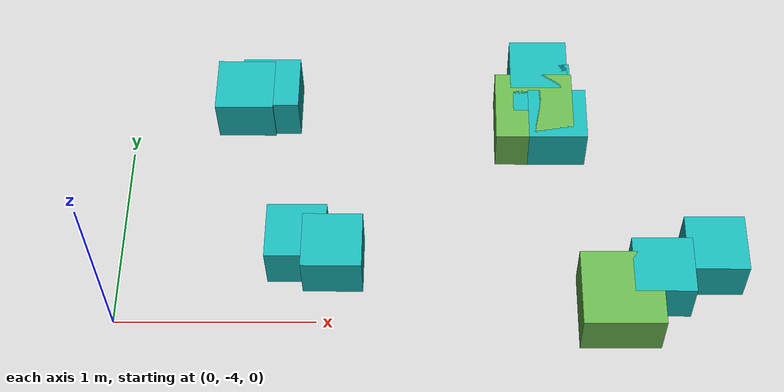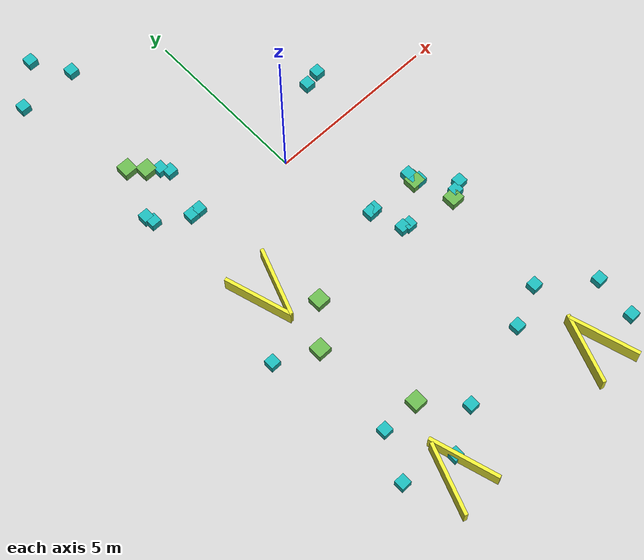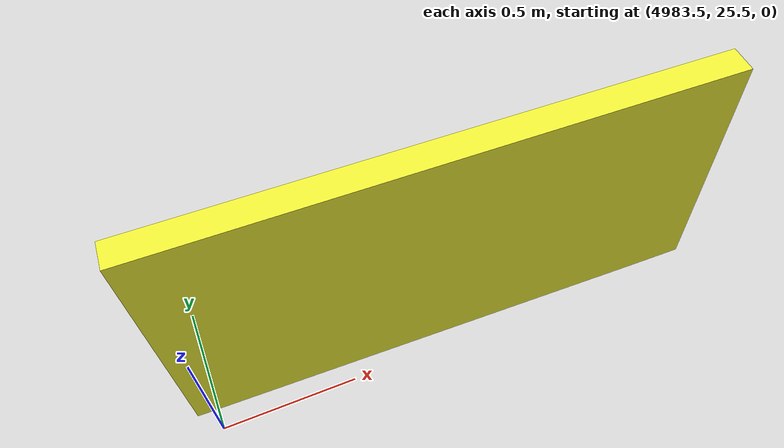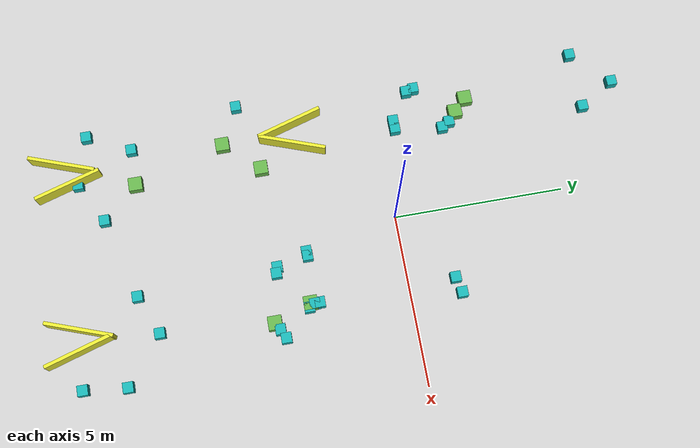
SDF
<sdf version="1.7">
 <world name="default">
  <scene><ambient>0.4 0.4 0.4 1</ambient><background>0.7 0.7 0.7 1</background><shadows>1</shadows></scene>
  <light name="sun" type="directional">
   <pose>0 0 10 0 -0 0</pose>
   <diffuse>0.8 0.8 0.8 1</diffuse>
   <specular>0.2 0.2 0.2 1</specular>
   <attenuation>
    <range>1000</range>
    <constant>0.9</constant>
    <linear>0.01</linear>
    <quadratic>0.001</quadratic>
   </attenuation>
   <direction>-0.5 0.1 -0.9</direction>
   <spot><inner_angle>0</inner_angle><outer_angle>0</outer_angle><falloff>0</falloff></spot>
  </light>
  <model name="ground_plane">
   <static>1</static>
   <link name="link">
    <collision name="collision">
     <geometry><plane><normal>0 0 1</normal><size>100 100</size></plane></geometry>
     <surface><friction><ode><mu>100</mu><mu2>50</mu2></ode></friction></surface>
    </collision>
    <visual name="visual">
     <cast_shadows>0</cast_shadows>
     <geometry><plane><normal>0 0 1</normal><size>100 100</size></plane></geometry>
     <material>
      <script><uri>file://media/materials/scripts/gazebo.material</uri><name>Gazebo/Grey</name></script>
     </material>
    </visual>
   </link>
  </model>
  <physics name="default_physics" default="0" type="ode">
   <real_time_update_rate>500000</real_time_update_rate>
   <max_step_size>0.02</max_step_size>
   <real_time_factor>0</real_time_factor>
   <ode>
    <solver>
     <type>quick</type>
     <iters>150</iters>
     <precon_iters>0</precon_iters>
     <sor>1.4</sor>
     <use_dynamic_moi_rescaling>1</use_dynamic_moi_rescaling>
    </solver>
    <constraints>
     <cfm>1e-05</cfm>
     <erp>0.2</erp>
     <contact_max_correcting_vel>2000</contact_max_correcting_vel>
     <contact_surface_layer>0.01</contact_surface_layer>
    </constraints>
   </ode>
  </physics>
  <gravity>0 0 -9.8</gravity>
  <magnetic_field>6e-06 2.3e-05 -4.2e-05</magnetic_field>
  <atmosphere type="adiabatic"/>
  <spherical_coordinates>
   <surface_model>EARTH_WGS84</surface_model>
   <latitude_deg>0</latitude_deg>
   <longitude_deg>0</longitude_deg>
   <elevation>0</elevation>
   <heading_deg>0</heading_deg>
  </spherical_coordinates>
  <audio><device>default</device></audio>
  <model name="wooden_wall_2_0">
   <link name="link_1">
    <inertial>
     <mass>1</mass>
     <inertia>
      <ixx>0.166667</ixx>
      <ixy>0</ixy>
      <ixz>0</ixz>
      <iyy>0.166667</iyy>
      <iyz>0</iyz>
      <izz>0.166667</izz>
     </inertia>
    </inertial>
    <visual name="visual">
     <geometry><box><size>2 0.1 1</size></box></geometry>
     <material>
      <lighting>1</lighting>
      <script><uri>file://media/materials/scripts/gazebo.material</uri><name>Gazebo/Grey</name></script>
      <shader type="pixel"><normal_map>__default__</normal_map></shader>
      <ambient>0.9 0.9 0.2 1</ambient>
      <diffuse>0.7 0.7 0.7 1</diffuse>
      <specular>0.01 0.01 0.01 1</specular>
      <emissive>0 0 0 1</emissive>
     </material>
    </visual>
    <collision name="collision">
     <geometry><box><size>2 0.1 1</size></box></geometry>
     <surface>
      <friction>
       <ode><mu>1</mu><mu2>1</mu2><fdir1>0 0 0</fdir1><slip1>0</slip1><slip2>0</slip2></ode>
       <torsional>
        <coefficient>1</coefficient>
        <patch_radius>0</patch_radius>
        <surface_radius>0</surface_radius>
        <use_patch_radius>1</use_patch_radius>
        <ode><slip>0</slip></ode>
       </torsional>
      </friction>
      <bounce><restitution_coefficient>0</restitution_coefficient><threshold>1e+06</threshold></bounce>
      <contact>
       <collide_without_contact>0</collide_without_contact>
       <collide_without_contact_bitmask>1</collide_without_contact_bitmask>
       <collide_bitmask>1</collide_bitmask>
       <ode>
        <soft_cfm>0</soft_cfm>
        <soft_erp>0.2</soft_erp>
        <kp>1e+13</kp>
        <kd>1</kd>
        <max_vel>0.01</max_vel>
        <min_depth>0</min_depth>
       </ode>
       <bullet>
        <split_impulse>1</split_impulse>
        <split_impulse_penetration_threshold>-0.01</split_impulse_penetration_threshold>
        <soft_cfm>0</soft_cfm>
        <soft_erp>0.2</soft_erp>
        <kp>1e+13</kp>
        <kd>1</kd>
       </bullet>
      </contact>
     </surface>
    </collision>
   </link>
   <static>0</static>
   <pose>4984.42 25.6101 0.489334 0.000254 -0.010782 -0.024175</pose>
  </model>
  <model name="unit_box_0.3_heavy">
   <link name="link">
    <inertial>
     <mass>100</mass>
     <inertia><ixx>1.5</ixx><ixy>0</ixy><ixz>0</ixz><iyy>1.5</iyy><iyz>0</iyz><izz>1.5</izz></inertia>
    </inertial>
    <visual name="visual">
     <geometry><box><size>0.3 0.3 0.5</size></box></geometry>
     <material>
      <script><name>Gazebo/Grey</name><uri>file://media/materials/scripts/gazebo.material</uri></script>
      <shader type="pixel"><normal_map>__default__</normal_map></shader>
      <ambient>0.1 0.7 0.7 1</ambient>
      <diffuse>0.7 0.7 0.7 1</diffuse>
      <specular>0.01 0.01 0.01 1</specular>
      <emissive>0 0 0 1</emissive>
     </material>
    </visual>
    <collision name="collision">
     <geometry><box><size>0.3 0.3 0.5</size></box></geometry>
     <surface>
      <friction>
       <ode><mu>1</mu><mu2>1</mu2><fdir1>0 0 0</fdir1><slip1>0</slip1><slip2>0</slip2></ode>
       <torsional>
        <coefficient>1</coefficient>
        <patch_radius>0</patch_radius>
        <surface_radius>0</surface_radius>
        <use_patch_radius>1</use_patch_radius>
        <ode><slip>0</slip></ode>
       </torsional>
      </friction>
      <bounce><restitution_coefficient>0</restitution_coefficient><threshold>1e+06</threshold></bounce>
      <contact>
       <collide_without_contact>0</collide_without_contact>
       <collide_without_contact_bitmask>1</collide_without_contact_bitmask>
       <collide_bitmask>1</collide_bitmask>
       <ode>
        <soft_cfm>0</soft_cfm>
        <soft_erp>0.2</soft_erp>
        <kp>1e+13</kp>
        <kd>1</kd>
        <max_vel>0.01</max_vel>
        <min_depth>0</min_depth>
       </ode>
       <bullet>
        <split_impulse>1</split_impulse>
        <split_impulse_penetration_threshold>-0.01</split_impulse_penetration_threshold>
        <soft_cfm>0</soft_cfm>
        <soft_erp>0.2</soft_erp>
        <kp>1e+13</kp>
        <kd>1</kd>
       </bullet>
      </contact>
     </surface>
    </collision>
   </link>
   <static>1</static>
   <pose>2.55116 1.46104 0 0 -0 0</pose>
  </model>
  <model name="unit_box_0.3_heavy_clone">
   <link name="link">
    <inertial>
     <mass>100</mass>
     <inertia><ixx>1.5</ixx><ixy>0</ixy><ixz>0</ixz><iyy>1.5</iyy><iyz>0</iyz><izz>1.5</izz></inertia>
    </inertial>
    <visual name="visual">
     <geometry><box><size>0.3 0.3 0.5</size></box></geometry>
     <material>
      <script><name>Gazebo/Grey</name><uri>file://media/materials/scripts/gazebo.material</uri></script>
      <shader type="pixel"><normal_map>__default__</normal_map></shader>
      <ambient>0.1 0.7 0.7 1</ambient>
      <diffuse>0.7 0.7 0.7 1</diffuse>
      <specular>0.01 0.01 0.01 1</specular>
      <emissive>0 0 0 1</emissive>
     </material>
    </visual>
    <collision name="collision">
     <geometry><box><size>0.3 0.3 0.5</size></box></geometry>
     <surface>
      <friction>
       <ode><mu>1</mu><mu2>1</mu2><fdir1>0 0 0</fdir1><slip1>0</slip1><slip2>0</slip2></ode>
       <torsional>
        <coefficient>1</coefficient>
        <patch_radius>0</patch_radius>
        <surface_radius>0</surface_radius>
        <use_patch_radius>1</use_patch_radius>
        <ode><slip>0</slip></ode>
       </torsional>
      </friction>
      <bounce><restitution_coefficient>0</restitution_coefficient><threshold>1e+06</threshold></bounce>
      <contact>
       <collide_without_contact>0</collide_without_contact>
       <collide_without_contact_bitmask>1</collide_without_contact_bitmask>
       <collide_bitmask>1</collide_bitmask>
       <ode>
        <soft_cfm>0</soft_cfm>
        <soft_erp>0.2</soft_erp>
        <kp>1e+13</kp>
        <kd>1</kd>
        <max_vel>0.01</max_vel>
        <min_depth>0</min_depth>
       </ode>
       <bullet>
        <split_impulse>1</split_impulse>
        <split_impulse_penetration_threshold>-0.01</split_impulse_penetration_threshold>
        <soft_cfm>0</soft_cfm>
        <soft_erp>0.2</soft_erp>
        <kp>1e+13</kp>
        <kd>1</kd>
       </bullet>
      </contact>
     </surface>
    </collision>
   </link>
   <static>1</static>
   <pose>2.08884 1.36124 0 0 -0 0</pose>
  </model>
  <model name="unit_box_0.3_heavy_clone_0">
   <link name="link">
    <inertial>
     <mass>100</mass>
     <inertia><ixx>1.5</ixx><ixy>0</ixy><ixz>0</ixz><iyy>1.5</iyy><iyz>0</iyz><izz>1.5</izz></inertia>
    </inertial>
    <visual name="visual">
     <geometry><box><size>0.3 0.3 0.5</size></box></geometry>
     <material>
      <script><name>Gazebo/Grey</name><uri>file://media/materials/scripts/gazebo.material</uri></script>
      <shader type="pixel"><normal_map>__default__</normal_map></shader>
      <ambient>0.1 0.7 0.7 1</ambient>
      <diffuse>0.7 0.7 0.7 1</diffuse>
      <specular>0.01 0.01 0.01 1</specular>
      <emissive>0 0 0 1</emissive>
     </material>
    </visual>
    <collision name="collision">
     <geometry><box><size>0.3 0.3 0.5</size></box></geometry>
     <surface>
      <friction>
       <ode><mu>1</mu><mu2>1</mu2><fdir1>0 0 0</fdir1><slip1>0</slip1><slip2>0</slip2></ode>
       <torsional>
        <coefficient>1</coefficient>
        <patch_radius>0</patch_radius>
        <surface_radius>0</surface_radius>
        <use_patch_radius>1</use_patch_radius>
        <ode><slip>0</slip></ode>
       </torsional>
      </friction>
      <bounce><restitution_coefficient>0</restitution_coefficient><threshold>1e+06</threshold></bounce>
      <contact>
       <collide_without_contact>0</collide_without_contact>
       <collide_without_contact_bitmask>1</collide_without_contact_bitmask>
       <collide_bitmask>1</collide_bitmask>
       <ode>
        <soft_cfm>0</soft_cfm>
        <soft_erp>0.2</soft_erp>
        <kp>1e+13</kp>
        <kd>1</kd>
        <max_vel>0.01</max_vel>
        <min_depth>0</min_depth>
       </ode>
       <bullet>
        <split_impulse>1</split_impulse>
        <split_impulse_penetration_threshold>-0.01</split_impulse_penetration_threshold>
        <soft_cfm>0</soft_cfm>
        <soft_erp>0.2</soft_erp>
        <kp>1e+13</kp>
        <kd>1</kd>
       </bullet>
      </contact>
     </surface>
    </collision>
   </link>
   <static>1</static>
   <pose>2.12804 -2.58503 0 0 -0 0</pose>
  </model>
  <model name="unit_box_0.3_heavy_clone_1">
   <link name="link">
    <inertial>
     <mass>100</mass>
     <inertia><ixx>1.5</ixx><ixy>0</ixy><ixz>0</ixz><iyy>1.5</iyy><iyz>0</iyz><izz>1.5</izz></inertia>
    </inertial>
    <visual name="visual">
     <geometry><box><size>0.3 0.3 0.5</size></box></geometry>
     <material>
      <script><name>Gazebo/Grey</name><uri>file://media/materials/scripts/gazebo.material</uri></script>
      <shader type="pixel"><normal_map>__default__</normal_map></shader>
      <ambient>0.1 0.7 0.7 1</ambient>
      <diffuse>0.7 0.7 0.7 1</diffuse>
      <specular>0.01 0.01 0.01 1</specular>
      <emissive>0 0 0 1</emissive>
     </material>
    </visual>
    <collision name="collision">
     <geometry><box><size>0.3 0.3 0.5</size></box></geometry>
     <surface>
      <friction>
       <ode><mu>1</mu><mu2>1</mu2><fdir1>0 0 0</fdir1><slip1>0</slip1><slip2>0</slip2></ode>
       <torsional>
        <coefficient>1</coefficient>
        <patch_radius>0</patch_radius>
        <surface_radius>0</surface_radius>
        <use_patch_radius>1</use_patch_radius>
        <ode><slip>0</slip></ode>
       </torsional>
      </friction>
      <bounce><restitution_coefficient>0</restitution_coefficient><threshold>1e+06</threshold></bounce>
      <contact>
       <collide_without_contact>0</collide_without_contact>
       <collide_without_contact_bitmask>1</collide_without_contact_bitmask>
       <collide_bitmask>1</collide_bitmask>
       <ode>
        <soft_cfm>0</soft_cfm>
        <soft_erp>0.2</soft_erp>
        <kp>1e+13</kp>
        <kd>1</kd>
        <max_vel>0.01</max_vel>
        <min_depth>0</min_depth>
       </ode>
       <bullet>
        <split_impulse>1</split_impulse>
        <split_impulse_penetration_threshold>-0.01</split_impulse_penetration_threshold>
        <soft_cfm>0</soft_cfm>
        <soft_erp>0.2</soft_erp>
        <kp>1e+13</kp>
        <kd>1</kd>
       </bullet>
      </contact>
     </surface>
    </collision>
   </link>
   <static>1</static>
   <pose>2.96818 -3.68438 0 0 -0 0</pose>
  </model>
  <model name="unit_box_0.3_heavy_clone_2">
   <link name="link">
    <inertial>
     <mass>100</mass>
     <inertia><ixx>1.5</ixx><ixy>0</ixy><ixz>0</ixz><iyy>1.5</iyy><iyz>0</iyz><izz>1.5</izz></inertia>
    </inertial>
    <visual name="visual">
     <geometry><box><size>0.3 0.3 0.5</size></box></geometry>
     <material>
      <script><name>Gazebo/Grey</name><uri>file://media/materials/scripts/gazebo.material</uri></script>
      <shader type="pixel"><normal_map>__default__</normal_map></shader>
      <ambient>0.1 0.7 0.7 1</ambient>
      <diffuse>0.7 0.7 0.7 1</diffuse>
      <specular>0.01 0.01 0.01 1</specular>
      <emissive>0 0 0 1</emissive>
     </material>
    </visual>
    <collision name="collision">
     <geometry><box><size>0.3 0.3 0.5</size></box></geometry>
     <surface>
      <friction>
       <ode><mu>1</mu><mu2>1</mu2><fdir1>0 0 0</fdir1><slip1>0</slip1><slip2>0</slip2></ode>
       <torsional>
        <coefficient>1</coefficient>
        <patch_radius>0</patch_radius>
        <surface_radius>0</surface_radius>
        <use_patch_radius>1</use_patch_radius>
        <ode><slip>0</slip></ode>
       </torsional>
      </friction>
      <bounce><restitution_coefficient>0</restitution_coefficient><threshold>1e+06</threshold></bounce>
      <contact>
       <collide_without_contact>0</collide_without_contact>
       <collide_without_contact_bitmask>1</collide_without_contact_bitmask>
       <collide_bitmask>1</collide_bitmask>
       <ode>
        <soft_cfm>0</soft_cfm>
        <soft_erp>0.2</soft_erp>
        <kp>1e+13</kp>
        <kd>1</kd>
        <max_vel>0.01</max_vel>
        <min_depth>0</min_depth>
       </ode>
       <bullet>
        <split_impulse>1</split_impulse>
        <split_impulse_penetration_threshold>-0.01</split_impulse_penetration_threshold>
        <soft_cfm>0</soft_cfm>
        <soft_erp>0.2</soft_erp>
        <kp>1e+13</kp>
        <kd>1</kd>
       </bullet>
      </contact>
     </surface>
    </collision>
   </link>
   <static>1</static>
   <pose>2.70017 -3.80803 0 0 -0 0</pose>
  </model>
  <model name="unit_box_0.3_heavy_clone_3">
   <link name="link">
    <inertial>
     <mass>100</mass>
     <inertia><ixx>1.5</ixx><ixy>0</ixy><ixz>0</ixz><iyy>1.5</iyy><iyz>0</iyz><izz>1.5</izz></inertia>
    </inertial>
    <visual name="visual">
     <geometry><box><size>0.3 0.3 0.5</size></box></geometry>
     <material>
      <script><name>Gazebo/Grey</name><uri>file://media/materials/scripts/gazebo.material</uri></script>
      <shader type="pixel"><normal_map>__default__</normal_map></shader>
      <ambient>0.1 0.7 0.7 1</ambient>
      <diffuse>0.7 0.7 0.7 1</diffuse>
      <specular>0.01 0.01 0.01 1</specular>
      <emissive>0 0 0 1</emissive>
     </material>
    </visual>
    <collision name="collision">
     <geometry><box><size>0.3 0.3 0.5</size></box></geometry>
     <surface>
      <friction>
       <ode><mu>1</mu><mu2>1</mu2><fdir1>0 0 0</fdir1><slip1>0</slip1><slip2>0</slip2></ode>
       <torsional>
        <coefficient>1</coefficient>
        <patch_radius>0</patch_radius>
        <surface_radius>0</surface_radius>
        <use_patch_radius>1</use_patch_radius>
        <ode><slip>0</slip></ode>
       </torsional>
      </friction>
      <bounce><restitution_coefficient>0</restitution_coefficient><threshold>1e+06</threshold></bounce>
      <contact>
       <collide_without_contact>0</collide_without_contact>
       <collide_without_contact_bitmask>1</collide_without_contact_bitmask>
       <collide_bitmask>1</collide_bitmask>
       <ode>
        <soft_cfm>0</soft_cfm>
        <soft_erp>0.2</soft_erp>
        <kp>1e+13</kp>
        <kd>1</kd>
        <max_vel>0.01</max_vel>
        <min_depth>0</min_depth>
       </ode>
       <bullet>
        <split_impulse>1</split_impulse>
        <split_impulse_penetration_threshold>-0.01</split_impulse_penetration_threshold>
        <soft_cfm>0</soft_cfm>
        <soft_erp>0.2</soft_erp>
        <kp>1e+13</kp>
        <kd>1</kd>
       </bullet>
      </contact>
     </surface>
    </collision>
   </link>
   <static>1</static>
   <pose>2.13984 -2.73394 0 0 -0 0</pose>
  </model>
  <model name="unit_box_0.3_heavy_clone_4">
   <link name="link">
    <inertial>
     <mass>100</mass>
     <inertia><ixx>1.5</ixx><ixy>0</ixy><ixz>0</ixz><iyy>1.5</iyy><iyz>0</iyz><izz>1.5</izz></inertia>
    </inertial>
    <visual name="visual">
     <geometry><box><size>0.3 0.3 0.5</size></box></geometry>
     <material>
      <script><name>Gazebo/Grey</name><uri>file://media/materials/scripts/gazebo.material</uri></script>
      <shader type="pixel"><normal_map>__default__</normal_map></shader>
      <ambient>0.1 0.7 0.7 1</ambient>
      <diffuse>0.7 0.7 0.7 1</diffuse>
      <specular>0.01 0.01 0.01 1</specular>
      <emissive>0 0 0 1</emissive>
     </material>
    </visual>
    <collision name="collision">
     <geometry><box><size>0.3 0.3 0.5</size></box></geometry>
     <surface>
      <friction>
       <ode><mu>1</mu><mu2>1</mu2><fdir1>0 0 0</fdir1><slip1>0</slip1><slip2>0</slip2></ode>
       <torsional>
        <coefficient>1</coefficient>
        <patch_radius>0</patch_radius>
        <surface_radius>0</surface_radius>
        <use_patch_radius>1</use_patch_radius>
        <ode><slip>0</slip></ode>
       </torsional>
      </friction>
      <bounce><restitution_coefficient>0</restitution_coefficient><threshold>1e+06</threshold></bounce>
      <contact>
       <collide_without_contact>0</collide_without_contact>
       <collide_without_contact_bitmask>1</collide_without_contact_bitmask>
       <collide_bitmask>1</collide_bitmask>
       <ode>
        <soft_cfm>0</soft_cfm>
        <soft_erp>0.2</soft_erp>
        <kp>1e+13</kp>
        <kd>1</kd>
        <max_vel>0.01</max_vel>
        <min_depth>0</min_depth>
       </ode>
       <bullet>
        <split_impulse>1</split_impulse>
        <split_impulse_penetration_threshold>-0.01</split_impulse_penetration_threshold>
        <soft_cfm>0</soft_cfm>
        <soft_erp>0.2</soft_erp>
        <kp>1e+13</kp>
        <kd>1</kd>
       </bullet>
      </contact>
     </surface>
    </collision>
   </link>
   <static>1</static>
   <pose>2.2171 -2.90142 0 0 -0 0</pose>
  </model>
  <model name="unit_box_0.3_heavy_clone_5">
   <link name="link">
    <inertial>
     <mass>100</mass>
     <inertia><ixx>1.5</ixx><ixy>0</ixy><ixz>0</ixz><iyy>1.5</iyy><iyz>0</iyz><izz>1.5</izz></inertia>
    </inertial>
    <visual name="visual">
     <geometry><box><size>0.3 0.3 0.5</size></box></geometry>
     <material>
      <script><name>Gazebo/Grey</name><uri>file://media/materials/scripts/gazebo.material</uri></script>
      <shader type="pixel"><normal_map>__default__</normal_map></shader>
      <ambient>0.1 0.7 0.7 1</ambient>
      <diffuse>0.7 0.7 0.7 1</diffuse>
      <specular>0.01 0.01 0.01 1</specular>
      <emissive>0 0 0 1</emissive>
     </material>
    </visual>
    <collision name="collision">
     <geometry><box><size>0.3 0.3 0.5</size></box></geometry>
     <surface>
      <friction>
       <ode><mu>1</mu><mu2>1</mu2><fdir1>0 0 0</fdir1><slip1>0</slip1><slip2>0</slip2></ode>
       <torsional>
        <coefficient>1</coefficient>
        <patch_radius>0</patch_radius>
        <surface_radius>0</surface_radius>
        <use_patch_radius>1</use_patch_radius>
        <ode><slip>0</slip></ode>
       </torsional>
      </friction>
      <bounce><restitution_coefficient>0</restitution_coefficient><threshold>1e+06</threshold></bounce>
      <contact>
       <collide_without_contact>0</collide_without_contact>
       <collide_without_contact_bitmask>1</collide_without_contact_bitmask>
       <collide_bitmask>1</collide_bitmask>
       <ode>
        <soft_cfm>0</soft_cfm>
        <soft_erp>0.2</soft_erp>
        <kp>1e+13</kp>
        <kd>1</kd>
        <max_vel>0.01</max_vel>
        <min_depth>0</min_depth>
       </ode>
       <bullet>
        <split_impulse>1</split_impulse>
        <split_impulse_penetration_threshold>-0.01</split_impulse_penetration_threshold>
        <soft_cfm>0</soft_cfm>
        <soft_erp>0.2</soft_erp>
        <kp>1e+13</kp>
        <kd>1</kd>
       </bullet>
      </contact>
     </surface>
    </collision>
   </link>
   <static>1</static>
   <pose>1.07636 -3.67231 0 0 -0 0</pose>
  </model>
  <model name="unit_box_0.3_heavy_clone_6">
   <link name="link">
    <inertial>
     <mass>100</mass>
     <inertia><ixx>1.5</ixx><ixy>0</ixy><ixz>0</ixz><iyy>1.5</iyy><iyz>0</iyz><izz>1.5</izz></inertia>
    </inertial>
    <visual name="visual">
     <geometry><box><size>0.3 0.3 0.5</size></box></geometry>
     <material>
      <script><name>Gazebo/Grey</name><uri>file://media/materials/scripts/gazebo.material</uri></script>
      <shader type="pixel"><normal_map>__default__</normal_map></shader>
      <ambient>0.1 0.7 0.7 1</ambient>
      <diffuse>0.7 0.7 0.7 1</diffuse>
      <specular>0.01 0.01 0.01 1</specular>
      <emissive>0 0 0 1</emissive>
     </material>
    </visual>
    <collision name="collision">
     <geometry><box><size>0.3 0.3 0.5</size></box></geometry>
     <surface>
      <friction>
       <ode><mu>1</mu><mu2>1</mu2><fdir1>0 0 0</fdir1><slip1>0</slip1><slip2>0</slip2></ode>
       <torsional>
        <coefficient>1</coefficient>
        <patch_radius>0</patch_radius>
        <surface_radius>0</surface_radius>
        <use_patch_radius>1</use_patch_radius>
        <ode><slip>0</slip></ode>
       </torsional>
      </friction>
      <bounce><restitution_coefficient>0</restitution_coefficient><threshold>1e+06</threshold></bounce>
      <contact>
       <collide_without_contact>0</collide_without_contact>
       <collide_without_contact_bitmask>1</collide_without_contact_bitmask>
       <collide_bitmask>1</collide_bitmask>
       <ode>
        <soft_cfm>0</soft_cfm>
        <soft_erp>0.2</soft_erp>
        <kp>1e+13</kp>
        <kd>1</kd>
        <max_vel>0.01</max_vel>
        <min_depth>0</min_depth>
       </ode>
       <bullet>
        <split_impulse>1</split_impulse>
        <split_impulse_penetration_threshold>-0.01</split_impulse_penetration_threshold>
        <soft_cfm>0</soft_cfm>
        <soft_erp>0.2</soft_erp>
        <kp>1e+13</kp>
        <kd>1</kd>
       </bullet>
      </contact>
     </surface>
    </collision>
   </link>
   <static>1</static>
   <pose>0.896545 -3.61717 0 0 -0 0</pose>
  </model>
  <model name="unit_box_0.3_heavy_clone_7">
   <link name="link">
    <inertial>
     <mass>100</mass>
     <inertia><ixx>1.5</ixx><ixy>0</ixy><ixz>0</ixz><iyy>1.5</iyy><iyz>0</iyz><izz>1.5</izz></inertia>
    </inertial>
    <visual name="visual">
     <geometry><box><size>0.3 0.3 0.5</size></box></geometry>
     <material>
      <script><name>Gazebo/Grey</name><uri>file://media/materials/scripts/gazebo.material</uri></script>
      <shader type="pixel"><normal_map>__default__</normal_map></shader>
      <ambient>0.1 0.7 0.7 1</ambient>
      <diffuse>0.7 0.7 0.7 1</diffuse>
      <specular>0.01 0.01 0.01 1</specular>
      <emissive>0 0 0 1</emissive>
     </material>
    </visual>
    <collision name="collision">
     <geometry><box><size>0.3 0.3 0.5</size></box></geometry>
     <surface>
      <friction>
       <ode><mu>1</mu><mu2>1</mu2><fdir1>0 0 0</fdir1><slip1>0</slip1><slip2>0</slip2></ode>
       <torsional>
        <coefficient>1</coefficient>
        <patch_radius>0</patch_radius>
        <surface_radius>0</surface_radius>
        <use_patch_radius>1</use_patch_radius>
        <ode><slip>0</slip></ode>
       </torsional>
      </friction>
      <bounce><restitution_coefficient>0</restitution_coefficient><threshold>1e+06</threshold></bounce>
      <contact>
       <collide_without_contact>0</collide_without_contact>
       <collide_without_contact_bitmask>1</collide_without_contact_bitmask>
       <collide_bitmask>1</collide_bitmask>
       <ode>
        <soft_cfm>0</soft_cfm>
        <soft_erp>0.2</soft_erp>
        <kp>1e+13</kp>
        <kd>1</kd>
        <max_vel>0.01</max_vel>
        <min_depth>0</min_depth>
       </ode>
       <bullet>
        <split_impulse>1</split_impulse>
        <split_impulse_penetration_threshold>-0.01</split_impulse_penetration_threshold>
        <soft_cfm>0</soft_cfm>
        <soft_erp>0.2</soft_erp>
        <kp>1e+13</kp>
        <kd>1</kd>
       </bullet>
      </contact>
     </surface>
    </collision>
   </link>
   <static>1</static>
   <pose>0.588928 -2.71749 0 0 -0 0</pose>
  </model>
  <model name="unit_box_0.3_heavy_clone_8">
   <link name="link">
    <inertial>
     <mass>100</mass>
     <inertia><ixx>1.5</ixx><ixy>0</ixy><ixz>0</ixz><iyy>1.5</iyy><iyz>0</iyz><izz>1.5</izz></inertia>
    </inertial>
    <visual name="visual">
     <geometry><box><size>0.3 0.3 0.5</size></box></geometry>
     <material>
      <script><name>Gazebo/Grey</name><uri>file://media/materials/scripts/gazebo.material</uri></script>
      <shader type="pixel"><normal_map>__default__</normal_map></shader>
      <ambient>0.1 0.7 0.7 1</ambient>
      <diffuse>0.7 0.7 0.7 1</diffuse>
      <specular>0.01 0.01 0.01 1</specular>
      <emissive>0 0 0 1</emissive>
     </material>
    </visual>
    <collision name="collision">
     <geometry><box><size>0.3 0.3 0.5</size></box></geometry>
     <surface>
      <friction>
       <ode><mu>1</mu><mu2>1</mu2><fdir1>0 0 0</fdir1><slip1>0</slip1><slip2>0</slip2></ode>
       <torsional>
        <coefficient>1</coefficient>
        <patch_radius>0</patch_radius>
        <surface_radius>0</surface_radius>
        <use_patch_radius>1</use_patch_radius>
        <ode><slip>0</slip></ode>
       </torsional>
      </friction>
      <bounce><restitution_coefficient>0</restitution_coefficient><threshold>1e+06</threshold></bounce>
      <contact>
       <collide_without_contact>0</collide_without_contact>
       <collide_without_contact_bitmask>1</collide_without_contact_bitmask>
       <collide_bitmask>1</collide_bitmask>
       <ode>
        <soft_cfm>0</soft_cfm>
        <soft_erp>0.2</soft_erp>
        <kp>1e+13</kp>
        <kd>1</kd>
        <max_vel>0.01</max_vel>
        <min_depth>0</min_depth>
       </ode>
       <bullet>
        <split_impulse>1</split_impulse>
        <split_impulse_penetration_threshold>-0.01</split_impulse_penetration_threshold>
        <soft_cfm>0</soft_cfm>
        <soft_erp>0.2</soft_erp>
        <kp>1e+13</kp>
        <kd>1</kd>
       </bullet>
      </contact>
     </surface>
    </collision>
   </link>
   <static>1</static>
   <pose>0.721323 -2.7051 0 0 -0 0</pose>
  </model>
  <model name="unit_box_0.3_heavy_clone_9">
   <link name="link">
    <inertial>
     <mass>100</mass>
     <inertia><ixx>1.5</ixx><ixy>0</ixy><ixz>0</ixz><iyy>1.5</iyy><iyz>0</iyz><izz>1.5</izz></inertia>
    </inertial>
    <visual name="visual">
     <geometry><box><size>0.3 0.3 0.5</size></box></geometry>
     <material>
      <script><name>Gazebo/Grey</name><uri>file://media/materials/scripts/gazebo.material</uri></script>
      <shader type="pixel"><normal_map>__default__</normal_map></shader>
      <ambient>0.1 0.7 0.7 1</ambient>
      <diffuse>0.7 0.7 0.7 1</diffuse>
      <specular>0.01 0.01 0.01 1</specular>
      <emissive>0 0 0 1</emissive>
     </material>
    </visual>
    <collision name="collision">
     <geometry><box><size>0.3 0.3 0.5</size></box></geometry>
     <surface>
      <friction>
       <ode><mu>1</mu><mu2>1</mu2><fdir1>0 0 0</fdir1><slip1>0</slip1><slip2>0</slip2></ode>
       <torsional>
        <coefficient>1</coefficient>
        <patch_radius>0</patch_radius>
        <surface_radius>0</surface_radius>
        <use_patch_radius>1</use_patch_radius>
        <ode><slip>0</slip></ode>
       </torsional>
      </friction>
      <bounce><restitution_coefficient>0</restitution_coefficient><threshold>1e+06</threshold></bounce>
      <contact>
       <collide_without_contact>0</collide_without_contact>
       <collide_without_contact_bitmask>1</collide_without_contact_bitmask>
       <collide_bitmask>1</collide_bitmask>
       <ode>
        <soft_cfm>0</soft_cfm>
        <soft_erp>0.2</soft_erp>
        <kp>1e+13</kp>
        <kd>1</kd>
        <max_vel>0.01</max_vel>
        <min_depth>0</min_depth>
       </ode>
       <bullet>
        <split_impulse>1</split_impulse>
        <split_impulse_penetration_threshold>-0.01</split_impulse_penetration_threshold>
        <soft_cfm>0</soft_cfm>
        <soft_erp>0.2</soft_erp>
        <kp>1e+13</kp>
        <kd>1</kd>
       </bullet>
      </contact>
     </surface>
    </collision>
   </link>
   <static>1</static>
   <pose>1.05115 -7.66638 0 0 -0 0</pose>
  </model>
  <model name="unit_box_0.3_heavy_clone_10">
   <link name="link">
    <inertial>
     <mass>100</mass>
     <inertia><ixx>1.5</ixx><ixy>0</ixy><ixz>0</ixz><iyy>1.5</iyy><iyz>0</iyz><izz>1.5</izz></inertia>
    </inertial>
    <visual name="visual">
     <geometry><box><size>0.3 0.3 0.5</size></box></geometry>
     <material>
      <script><name>Gazebo/Grey</name><uri>file://media/materials/scripts/gazebo.material</uri></script>
      <shader type="pixel"><normal_map>__default__</normal_map></shader>
      <ambient>0.1 0.7 0.7 1</ambient>
      <diffuse>0.7 0.7 0.7 1</diffuse>
      <specular>0.01 0.01 0.01 1</specular>
      <emissive>0 0 0 1</emissive>
     </material>
    </visual>
    <collision name="collision">
     <geometry><box><size>0.3 0.3 0.5</size></box></geometry>
     <surface>
      <friction>
       <ode><mu>1</mu><mu2>1</mu2><fdir1>0 0 0</fdir1><slip1>0</slip1><slip2>0</slip2></ode>
       <torsional>
        <coefficient>1</coefficient>
        <patch_radius>0</patch_radius>
        <surface_radius>0</surface_radius>
        <use_patch_radius>1</use_patch_radius>
        <ode><slip>0</slip></ode>
       </torsional>
      </friction>
      <bounce><restitution_coefficient>0</restitution_coefficient><threshold>1e+06</threshold></bounce>
      <contact>
       <collide_without_contact>0</collide_without_contact>
       <collide_without_contact_bitmask>1</collide_without_contact_bitmask>
       <collide_bitmask>1</collide_bitmask>
       <ode>
        <soft_cfm>0</soft_cfm>
        <soft_erp>0.2</soft_erp>
        <kp>1e+13</kp>
        <kd>1</kd>
        <max_vel>0.01</max_vel>
        <min_depth>0</min_depth>
       </ode>
       <bullet>
        <split_impulse>1</split_impulse>
        <split_impulse_penetration_threshold>-0.01</split_impulse_penetration_threshold>
        <soft_cfm>0</soft_cfm>
        <soft_erp>0.2</soft_erp>
        <kp>1e+13</kp>
        <kd>1</kd>
       </bullet>
      </contact>
     </surface>
    </collision>
   </link>
   <static>1</static>
   <pose>2.20551 -7.17477 0 0 -0 0</pose>
  </model>
  <model name="unit_box_0.3_heavy_clone_11">
   <link name="link">
    <inertial>
     <mass>100</mass>
     <inertia><ixx>1.5</ixx><ixy>0</ixy><ixz>0</ixz><iyy>1.5</iyy><iyz>0</iyz><izz>1.5</izz></inertia>
    </inertial>
    <visual name="visual">
     <geometry><box><size>0.3 0.3 0.5</size></box></geometry>
     <material>
      <script><name>Gazebo/Grey</name><uri>file://media/materials/scripts/gazebo.material</uri></script>
      <shader type="pixel"><normal_map>__default__</normal_map></shader>
      <ambient>0.1 0.7 0.7 1</ambient>
      <diffuse>0.7 0.7 0.7 1</diffuse>
      <specular>0.01 0.01 0.01 1</specular>
      <emissive>0 0 0 1</emissive>
     </material>
    </visual>
    <collision name="collision">
     <geometry><box><size>0.3 0.3 0.5</size></box></geometry>
     <surface>
      <friction>
       <ode><mu>1</mu><mu2>1</mu2><fdir1>0 0 0</fdir1><slip1>0</slip1><slip2>0</slip2></ode>
       <torsional>
        <coefficient>1</coefficient>
        <patch_radius>0</patch_radius>
        <surface_radius>0</surface_radius>
        <use_patch_radius>1</use_patch_radius>
        <ode><slip>0</slip></ode>
       </torsional>
      </friction>
      <bounce><restitution_coefficient>0</restitution_coefficient><threshold>1e+06</threshold></bounce>
      <contact>
       <collide_without_contact>0</collide_without_contact>
       <collide_without_contact_bitmask>1</collide_without_contact_bitmask>
       <collide_bitmask>1</collide_bitmask>
       <ode>
        <soft_cfm>0</soft_cfm>
        <soft_erp>0.2</soft_erp>
        <kp>1e+13</kp>
        <kd>1</kd>
        <max_vel>0.01</max_vel>
        <min_depth>0</min_depth>
       </ode>
       <bullet>
        <split_impulse>1</split_impulse>
        <split_impulse_penetration_threshold>-0.01</split_impulse_penetration_threshold>
        <soft_cfm>0</soft_cfm>
        <soft_erp>0.2</soft_erp>
        <kp>1e+13</kp>
        <kd>1</kd>
       </bullet>
      </contact>
     </surface>
    </collision>
   </link>
   <static>1</static>
   <pose>3.55898 -8.2246 0 0 -0 0</pose>
  </model>
  <model name="unit_box_0.3_heavy_clone_12">
   <link name="link">
    <inertial>
     <mass>100</mass>
     <inertia><ixx>1.5</ixx><ixy>0</ixy><ixz>0</ixz><iyy>1.5</iyy><iyz>0</iyz><izz>1.5</izz></inertia>
    </inertial>
    <visual name="visual">
     <geometry><box><size>0.3 0.3 0.5</size></box></geometry>
     <material>
      <script><name>Gazebo/Grey</name><uri>file://media/materials/scripts/gazebo.material</uri></script>
      <shader type="pixel"><normal_map>__default__</normal_map></shader>
      <ambient>0.1 0.7 0.7 1</ambient>
      <diffuse>0.7 0.7 0.7 1</diffuse>
      <specular>0.01 0.01 0.01 1</specular>
      <emissive>0 0 0 1</emissive>
     </material>
    </visual>
    <collision name="collision">
     <geometry><box><size>0.3 0.3 0.5</size></box></geometry>
     <surface>
      <friction>
       <ode><mu>1</mu><mu2>1</mu2><fdir1>0 0 0</fdir1><slip1>0</slip1><slip2>0</slip2></ode>
       <torsional>
        <coefficient>1</coefficient>
        <patch_radius>0</patch_radius>
        <surface_radius>0</surface_radius>
        <use_patch_radius>1</use_patch_radius>
        <ode><slip>0</slip></ode>
       </torsional>
      </friction>
      <bounce><restitution_coefficient>0</restitution_coefficient><threshold>1e+06</threshold></bounce>
      <contact>
       <collide_without_contact>0</collide_without_contact>
       <collide_without_contact_bitmask>1</collide_without_contact_bitmask>
       <collide_bitmask>1</collide_bitmask>
       <ode>
        <soft_cfm>0</soft_cfm>
        <soft_erp>0.2</soft_erp>
        <kp>1e+13</kp>
        <kd>1</kd>
        <max_vel>0.01</max_vel>
        <min_depth>0</min_depth>
       </ode>
       <bullet>
        <split_impulse>1</split_impulse>
        <split_impulse_penetration_threshold>-0.01</split_impulse_penetration_threshold>
        <soft_cfm>0</soft_cfm>
        <soft_erp>0.2</soft_erp>
        <kp>1e+13</kp>
        <kd>1</kd>
       </bullet>
      </contact>
     </surface>
    </collision>
   </link>
   <static>1</static>
   <pose>3.42044 -9.47445 0 0 -0 0</pose>
  </model>
  <model name="wooden_wall_2_heavy">
   <link name="link_1">
    <inertial>
     <mass>100</mass>
     <inertia><ixx>8.41667</ixx><ixy>0</ixy><ixz>0</ixz><iyy>41.6667</iyy><iyz>0</iyz><izz>33.4167</izz></inertia>
    </inertial>
    <visual name="visual">
     <geometry><box><size>2 0.1 1</size></box></geometry>
     <material>
      <lighting>1</lighting>
      <script><uri>file://media/materials/scripts/gazebo.material</uri><name>Gazebo/Grey</name></script>
      <shader type="pixel"><normal_map>__default__</normal_map></shader>
      <ambient>0.9 0.9 0.2 1</ambient>
      <diffuse>0.7 0.7 0.7 1</diffuse>
      <specular>0.01 0.01 0.01 1</specular>
      <emissive>0 0 0 1</emissive>
     </material>
    </visual>
    <collision name="collision">
     <geometry><box><size>2 0.1 1</size></box></geometry>
     <surface>
      <friction>
       <ode><mu>1</mu><mu2>1</mu2><fdir1>0 0 0</fdir1><slip1>0</slip1><slip2>0</slip2></ode>
       <torsional>
        <coefficient>1</coefficient>
        <patch_radius>0</patch_radius>
        <surface_radius>0</surface_radius>
        <use_patch_radius>1</use_patch_radius>
        <ode><slip>0</slip></ode>
       </torsional>
      </friction>
      <bounce><restitution_coefficient>0</restitution_coefficient><threshold>1e+06</threshold></bounce>
      <contact>
       <collide_without_contact>0</collide_without_contact>
       <collide_without_contact_bitmask>1</collide_without_contact_bitmask>
       <collide_bitmask>1</collide_bitmask>
       <ode>
        <soft_cfm>0</soft_cfm>
        <soft_erp>0.2</soft_erp>
        <kp>1e+13</kp>
        <kd>1</kd>
        <max_vel>0.01</max_vel>
        <min_depth>0</min_depth>
       </ode>
       <bullet>
        <split_impulse>1</split_impulse>
        <split_impulse_penetration_threshold>-0.01</split_impulse_penetration_threshold>
        <soft_cfm>0</soft_cfm>
        <soft_erp>0.2</soft_erp>
        <kp>1e+13</kp>
        <kd>1</kd>
       </bullet>
      </contact>
     </surface>
    </collision>
   </link>
   <static>1</static>
   <allow_auto_disable>0</allow_auto_disable>
   <pose>1.74439 -9.35521 0 0 -0 1.22167</pose>
  </model>
  <model name="wooden_wall_2_heavy_clone">
   <link name="link_1">
    <inertial>
     <mass>100</mass>
     <inertia><ixx>8.41667</ixx><ixy>0</ixy><ixz>0</ixz><iyy>41.6667</iyy><iyz>0</iyz><izz>33.4167</izz></inertia>
    </inertial>
    <visual name="visual">
     <geometry><box><size>2 0.1 1</size></box></geometry>
     <material>
      <lighting>1</lighting>
      <script><uri>file://media/materials/scripts/gazebo.material</uri><name>Gazebo/Grey</name></script>
      <shader type="pixel"><normal_map>__default__</normal_map></shader>
      <ambient>0.9 0.9 0.2 1</ambient>
      <diffuse>0.7 0.7 0.7 1</diffuse>
      <specular>0.01 0.01 0.01 1</specular>
      <emissive>0 0 0 1</emissive>
     </material>
    </visual>
    <collision name="collision">
     <geometry><box><size>2 0.1 1</size></box></geometry>
     <surface>
      <friction>
       <ode><mu>1</mu><mu2>1</mu2><fdir1>0 0 0</fdir1><slip1>0</slip1><slip2>0</slip2></ode>
       <torsional>
        <coefficient>1</coefficient>
        <patch_radius>0</patch_radius>
        <surface_radius>0</surface_radius>
        <use_patch_radius>1</use_patch_radius>
        <ode><slip>0</slip></ode>
       </torsional>
      </friction>
      <bounce><restitution_coefficient>0</restitution_coefficient><threshold>1e+06</threshold></bounce>
      <contact>
       <collide_without_contact>0</collide_without_contact>
       <collide_without_contact_bitmask>1</collide_without_contact_bitmask>
       <collide_bitmask>1</collide_bitmask>
       <ode>
        <soft_cfm>0</soft_cfm>
        <soft_erp>0.2</soft_erp>
        <kp>1e+13</kp>
        <kd>1</kd>
        <max_vel>0.01</max_vel>
        <min_depth>0</min_depth>
       </ode>
       <bullet>
        <split_impulse>1</split_impulse>
        <split_impulse_penetration_threshold>-0.01</split_impulse_penetration_threshold>
        <soft_cfm>0</soft_cfm>
        <soft_erp>0.2</soft_erp>
        <kp>1e+13</kp>
        <kd>1</kd>
       </bullet>
      </contact>
     </surface>
    </collision>
   </link>
   <static>1</static>
   <allow_auto_disable>0</allow_auto_disable>
   <pose>2.34834 -9.44014 0 0 -0 1.86218</pose>
  </model>
  <model name="unit_box_0.3_heavy_clone_clone">
   <link name="link">
    <inertial>
     <mass>100</mass>
     <inertia><ixx>1.5</ixx><ixy>0</ixy><ixz>0</ixz><iyy>1.5</iyy><iyz>0</iyz><izz>1.5</izz></inertia>
    </inertial>
    <visual name="visual">
     <geometry><box><size>0.3 0.3 0.5</size></box></geometry>
     <material>
      <script><name>Gazebo/Grey</name><uri>file://media/materials/scripts/gazebo.material</uri></script>
      <shader type="pixel"><normal_map>__default__</normal_map></shader>
      <ambient>0.1 0.7 0.7 1</ambient>
      <diffuse>0.7 0.7 0.7 1</diffuse>
      <specular>0.01 0.01 0.01 1</specular>
      <emissive>0 0 0 1</emissive>
     </material>
    </visual>
    <collision name="collision">
     <geometry><box><size>0.3 0.3 0.5</size></box></geometry>
     <surface>
      <friction>
       <ode><mu>1</mu><mu2>1</mu2><fdir1>0 0 0</fdir1><slip1>0</slip1><slip2>0</slip2></ode>
       <torsional>
        <coefficient>1</coefficient>
        <patch_radius>0</patch_radius>
        <surface_radius>0</surface_radius>
        <use_patch_radius>1</use_patch_radius>
        <ode><slip>0</slip></ode>
       </torsional>
      </friction>
      <bounce><restitution_coefficient>0</restitution_coefficient><threshold>1e+06</threshold></bounce>
      <contact>
       <collide_without_contact>0</collide_without_contact>
       <collide_without_contact_bitmask>1</collide_without_contact_bitmask>
       <collide_bitmask>1</collide_bitmask>
       <ode>
        <soft_cfm>0</soft_cfm>
        <soft_erp>0.2</soft_erp>
        <kp>1e+13</kp>
        <kd>1</kd>
        <max_vel>0.01</max_vel>
        <min_depth>0</min_depth>
       </ode>
       <bullet>
        <split_impulse>1</split_impulse>
        <split_impulse_penetration_threshold>-0.01</split_impulse_penetration_threshold>
        <soft_cfm>0</soft_cfm>
        <soft_erp>0.2</soft_erp>
        <kp>1e+13</kp>
        <kd>1</kd>
       </bullet>
      </contact>
     </surface>
    </collision>
   </link>
   <static>1</static>
   <pose>-3.0247 7.2506 0 0 -0 0</pose>
  </model>
  <model name="unit_box_0.3_heavy_clone_clone_0">
   <link name="link">
    <inertial>
     <mass>100</mass>
     <inertia><ixx>1.5</ixx><ixy>0</ixy><ixz>0</ixz><iyy>1.5</iyy><iyz>0</iyz><izz>1.5</izz></inertia>
    </inertial>
    <visual name="visual">
     <geometry><box><size>0.3 0.3 0.5</size></box></geometry>
     <material>
      <script><name>Gazebo/Grey</name><uri>file://media/materials/scripts/gazebo.material</uri></script>
      <shader type="pixel"><normal_map>__default__</normal_map></shader>
      <ambient>0.1 0.7 0.7 1</ambient>
      <diffuse>0.7 0.7 0.7 1</diffuse>
      <specular>0.01 0.01 0.01 1</specular>
      <emissive>0 0 0 1</emissive>
     </material>
    </visual>
    <collision name="collision">
     <geometry><box><size>0.3 0.3 0.5</size></box></geometry>
     <surface>
      <friction>
       <ode><mu>1</mu><mu2>1</mu2><fdir1>0 0 0</fdir1><slip1>0</slip1><slip2>0</slip2></ode>
       <torsional>
        <coefficient>1</coefficient>
        <patch_radius>0</patch_radius>
        <surface_radius>0</surface_radius>
        <use_patch_radius>1</use_patch_radius>
        <ode><slip>0</slip></ode>
       </torsional>
      </friction>
      <bounce><restitution_coefficient>0</restitution_coefficient><threshold>1e+06</threshold></bounce>
      <contact>
       <collide_without_contact>0</collide_without_contact>
       <collide_without_contact_bitmask>1</collide_without_contact_bitmask>
       <collide_bitmask>1</collide_bitmask>
       <ode>
        <soft_cfm>0</soft_cfm>
        <soft_erp>0.2</soft_erp>
        <kp>1e+13</kp>
        <kd>1</kd>
        <max_vel>0.01</max_vel>
        <min_depth>0</min_depth>
       </ode>
       <bullet>
        <split_impulse>1</split_impulse>
        <split_impulse_penetration_threshold>-0.01</split_impulse_penetration_threshold>
        <soft_cfm>0</soft_cfm>
        <soft_erp>0.2</soft_erp>
        <kp>1e+13</kp>
        <kd>1</kd>
       </bullet>
      </contact>
     </surface>
    </collision>
   </link>
   <static>1</static>
   <pose>-4.09696 6.21186 0 0 -0 0</pose>
  </model>
  <model name="unit_box_0.3_heavy_clone_clone_1">
   <link name="link">
    <inertial>
     <mass>100</mass>
     <inertia><ixx>1.5</ixx><ixy>0</ixy><ixz>0</ixz><iyy>1.5</iyy><iyz>0</iyz><izz>1.5</izz></inertia>
    </inertial>
    <visual name="visual">
     <geometry><box><size>0.3 0.3 0.5</size></box></geometry>
     <material>
      <script><name>Gazebo/Grey</name><uri>file://media/materials/scripts/gazebo.material</uri></script>
      <shader type="pixel"><normal_map>__default__</normal_map></shader>
      <ambient>0.1 0.7 0.7 1</ambient>
      <diffuse>0.7 0.7 0.7 1</diffuse>
      <specular>0.01 0.01 0.01 1</specular>
      <emissive>0 0 0 1</emissive>
     </material>
    </visual>
    <collision name="collision">
     <geometry><box><size>0.3 0.3 0.5</size></box></geometry>
     <surface>
      <friction>
       <ode><mu>1</mu><mu2>1</mu2><fdir1>0 0 0</fdir1><slip1>0</slip1><slip2>0</slip2></ode>
       <torsional>
        <coefficient>1</coefficient>
        <patch_radius>0</patch_radius>
        <surface_radius>0</surface_radius>
        <use_patch_radius>1</use_patch_radius>
        <ode><slip>0</slip></ode>
       </torsional>
      </friction>
      <bounce><restitution_coefficient>0</restitution_coefficient><threshold>1e+06</threshold></bounce>
      <contact>
       <collide_without_contact>0</collide_without_contact>
       <collide_without_contact_bitmask>1</collide_without_contact_bitmask>
       <collide_bitmask>1</collide_bitmask>
       <ode>
        <soft_cfm>0</soft_cfm>
        <soft_erp>0.2</soft_erp>
        <kp>1e+13</kp>
        <kd>1</kd>
        <max_vel>0.01</max_vel>
        <min_depth>0</min_depth>
       </ode>
       <bullet>
        <split_impulse>1</split_impulse>
        <split_impulse_penetration_threshold>-0.01</split_impulse_penetration_threshold>
        <soft_cfm>0</soft_cfm>
        <soft_erp>0.2</soft_erp>
        <kp>1e+13</kp>
        <kd>1</kd>
       </bullet>
      </contact>
     </surface>
    </collision>
   </link>
   <static>1</static>
   <pose>-2.39763 6.20785 0 0 -0 0</pose>
  </model>
  <model name="unit_box_0.3_heavy_clone_clone_2">
   <link name="link">
    <inertial>
     <mass>100</mass>
     <inertia><ixx>1.5</ixx><ixy>0</ixy><ixz>0</ixz><iyy>1.5</iyy><iyz>0</iyz><izz>1.5</izz></inertia>
    </inertial>
    <visual name="visual">
     <geometry><box><size>0.3 0.3 0.5</size></box></geometry>
     <material>
      <script><name>Gazebo/Grey</name><uri>file://media/materials/scripts/gazebo.material</uri></script>
      <shader type="pixel"><normal_map>__default__</normal_map></shader>
      <ambient>0.1 0.7 0.7 1</ambient>
      <diffuse>0.7 0.7 0.7 1</diffuse>
      <specular>0.01 0.01 0.01 1</specular>
      <emissive>0 0 0 1</emissive>
     </material>
    </visual>
    <collision name="collision">
     <geometry><box><size>0.3 0.3 0.5</size></box></geometry>
     <surface>
      <friction>
       <ode><mu>1</mu><mu2>1</mu2><fdir1>0 0 0</fdir1><slip1>0</slip1><slip2>0</slip2></ode>
       <torsional>
        <coefficient>1</coefficient>
        <patch_radius>0</patch_radius>
        <surface_radius>0</surface_radius>
        <use_patch_radius>1</use_patch_radius>
        <ode><slip>0</slip></ode>
       </torsional>
      </friction>
      <bounce><restitution_coefficient>0</restitution_coefficient><threshold>1e+06</threshold></bounce>
      <contact>
       <collide_without_contact>0</collide_without_contact>
       <collide_without_contact_bitmask>1</collide_without_contact_bitmask>
       <collide_bitmask>1</collide_bitmask>
       <ode>
        <soft_cfm>0</soft_cfm>
        <soft_erp>0.2</soft_erp>
        <kp>1e+13</kp>
        <kd>1</kd>
        <max_vel>0.01</max_vel>
        <min_depth>0</min_depth>
       </ode>
       <bullet>
        <split_impulse>1</split_impulse>
        <split_impulse_penetration_threshold>-0.01</split_impulse_penetration_threshold>
        <soft_cfm>0</soft_cfm>
        <soft_erp>0.2</soft_erp>
        <kp>1e+13</kp>
        <kd>1</kd>
       </bullet>
      </contact>
     </surface>
    </collision>
   </link>
   <static>1</static>
   <pose>-2.61463 2.15152 0 0 -0 0</pose>
  </model>
  <model name="unit_box_0.3_heavy_clone_clone_3">
   <link name="link">
    <inertial>
     <mass>100</mass>
     <inertia><ixx>1.5</ixx><ixy>0</ixy><ixz>0</ixz><iyy>1.5</iyy><iyz>0</iyz><izz>1.5</izz></inertia>
    </inertial>
    <visual name="visual">
     <geometry><box><size>0.3 0.3 0.5</size></box></geometry>
     <material>
      <script><name>Gazebo/Grey</name><uri>file://media/materials/scripts/gazebo.material</uri></script>
      <shader type="pixel"><normal_map>__default__</normal_map></shader>
      <ambient>0.1 0.7 0.7 1</ambient>
      <diffuse>0.7 0.7 0.7 1</diffuse>
      <specular>0.01 0.01 0.01 1</specular>
      <emissive>0 0 0 1</emissive>
     </material>
    </visual>
    <collision name="collision">
     <geometry><box><size>0.3 0.3 0.5</size></box></geometry>
     <surface>
      <friction>
       <ode><mu>1</mu><mu2>1</mu2><fdir1>0 0 0</fdir1><slip1>0</slip1><slip2>0</slip2></ode>
       <torsional>
        <coefficient>1</coefficient>
        <patch_radius>0</patch_radius>
        <surface_radius>0</surface_radius>
        <use_patch_radius>1</use_patch_radius>
        <ode><slip>0</slip></ode>
       </torsional>
      </friction>
      <bounce><restitution_coefficient>0</restitution_coefficient><threshold>1e+06</threshold></bounce>
      <contact>
       <collide_without_contact>0</collide_without_contact>
       <collide_without_contact_bitmask>1</collide_without_contact_bitmask>
       <collide_bitmask>1</collide_bitmask>
       <ode>
        <soft_cfm>0</soft_cfm>
        <soft_erp>0.2</soft_erp>
        <kp>1e+13</kp>
        <kd>1</kd>
        <max_vel>0.01</max_vel>
        <min_depth>0</min_depth>
       </ode>
       <bullet>
        <split_impulse>1</split_impulse>
        <split_impulse_penetration_threshold>-0.01</split_impulse_penetration_threshold>
        <soft_cfm>0</soft_cfm>
        <soft_erp>0.2</soft_erp>
        <kp>1e+13</kp>
        <kd>1</kd>
       </bullet>
      </contact>
     </surface>
    </collision>
   </link>
   <static>1</static>
   <pose>-3.84609 1.29928 0 0 -0 0</pose>
  </model>
  <model name="unit_box_0.3_heavy_clone_clone_4">
   <link name="link">
    <inertial>
     <mass>100</mass>
     <inertia><ixx>1.5</ixx><ixy>0</ixy><ixz>0</ixz><iyy>1.5</iyy><iyz>0</iyz><izz>1.5</izz></inertia>
    </inertial>
    <visual name="visual">
     <geometry><box><size>0.3 0.3 0.5</size></box></geometry>
     <material>
      <script><name>Gazebo/Grey</name><uri>file://media/materials/scripts/gazebo.material</uri></script>
      <shader type="pixel"><normal_map>__default__</normal_map></shader>
      <ambient>0.1 0.7 0.7 1</ambient>
      <diffuse>0.7 0.7 0.7 1</diffuse>
      <specular>0.01 0.01 0.01 1</specular>
      <emissive>0 0 0 1</emissive>
     </material>
    </visual>
    <collision name="collision">
     <geometry><box><size>0.3 0.3 0.5</size></box></geometry>
     <surface>
      <friction>
       <ode><mu>1</mu><mu2>1</mu2><fdir1>0 0 0</fdir1><slip1>0</slip1><slip2>0</slip2></ode>
       <torsional>
        <coefficient>1</coefficient>
        <patch_radius>0</patch_radius>
        <surface_radius>0</surface_radius>
        <use_patch_radius>1</use_patch_radius>
        <ode><slip>0</slip></ode>
       </torsional>
      </friction>
      <bounce><restitution_coefficient>0</restitution_coefficient><threshold>1e+06</threshold></bounce>
      <contact>
       <collide_without_contact>0</collide_without_contact>
       <collide_without_contact_bitmask>1</collide_without_contact_bitmask>
       <collide_bitmask>1</collide_bitmask>
       <ode>
        <soft_cfm>0</soft_cfm>
        <soft_erp>0.2</soft_erp>
        <kp>1e+13</kp>
        <kd>1</kd>
        <max_vel>0.01</max_vel>
        <min_depth>0</min_depth>
       </ode>
       <bullet>
        <split_impulse>1</split_impulse>
        <split_impulse_penetration_threshold>-0.01</split_impulse_penetration_threshold>
        <soft_cfm>0</soft_cfm>
        <soft_erp>0.2</soft_erp>
        <kp>1e+13</kp>
        <kd>1</kd>
       </bullet>
      </contact>
     </surface>
    </collision>
   </link>
   <static>1</static>
   <pose>-2.47359 1.91605 0 0 -0 0</pose>
  </model>
  <model name="unit_box_0.3_heavy_clone_clone_5">
   <link name="link">
    <inertial>
     <mass>100</mass>
     <inertia><ixx>1.5</ixx><ixy>0</ixy><ixz>0</ixz><iyy>1.5</iyy><iyz>0</iyz><izz>1.5</izz></inertia>
    </inertial>
    <visual name="visual">
     <geometry><box><size>0.3 0.3 0.5</size></box></geometry>
     <material>
      <script><name>Gazebo/Grey</name><uri>file://media/materials/scripts/gazebo.material</uri></script>
      <shader type="pixel"><normal_map>__default__</normal_map></shader>
      <ambient>0.1 0.7 0.7 1</ambient>
      <diffuse>0.7 0.7 0.7 1</diffuse>
      <specular>0.01 0.01 0.01 1</specular>
      <emissive>0 0 0 1</emissive>
     </material>
    </visual>
    <collision name="collision">
     <geometry><box><size>0.3 0.3 0.5</size></box></geometry>
     <surface>
      <friction>
       <ode><mu>1</mu><mu2>1</mu2><fdir1>0 0 0</fdir1><slip1>0</slip1><slip2>0</slip2></ode>
       <torsional>
        <coefficient>1</coefficient>
        <patch_radius>0</patch_radius>
        <surface_radius>0</surface_radius>
        <use_patch_radius>1</use_patch_radius>
        <ode><slip>0</slip></ode>
       </torsional>
      </friction>
      <bounce><restitution_coefficient>0</restitution_coefficient><threshold>1e+06</threshold></bounce>
      <contact>
       <collide_without_contact>0</collide_without_contact>
       <collide_without_contact_bitmask>1</collide_without_contact_bitmask>
       <collide_bitmask>1</collide_bitmask>
       <ode>
        <soft_cfm>0</soft_cfm>
        <soft_erp>0.2</soft_erp>
        <kp>1e+13</kp>
        <kd>1</kd>
        <max_vel>0.01</max_vel>
        <min_depth>0</min_depth>
       </ode>
       <bullet>
        <split_impulse>1</split_impulse>
        <split_impulse_penetration_threshold>-0.01</split_impulse_penetration_threshold>
        <soft_cfm>0</soft_cfm>
        <soft_erp>0.2</soft_erp>
        <kp>1e+13</kp>
        <kd>1</kd>
       </bullet>
      </contact>
     </surface>
    </collision>
   </link>
   <static>1</static>
   <pose>-3.78741 1.06644 0 0 -0 0</pose>
  </model>
  <model name="unit_box_0.4_heavy_clone">
   <link name="link">
    <inertial>
     <mass>100</mass>
     <inertia><ixx>1.5</ixx><ixy>0</ixy><ixz>0</ixz><iyy>1.5</iyy><iyz>0</iyz><izz>1.5</izz></inertia>
    </inertial>
    <visual name="visual">
     <geometry><box><size>0.4 0.4 0.5</size></box></geometry>
     <material>
      <script><name>Gazebo/Grey</name><uri>file://media/materials/scripts/gazebo.material</uri></script>
      <shader type="pixel"><normal_map>__default__</normal_map></shader>
      <ambient>0.4 0.7 0.3 1</ambient>
      <diffuse>0.7 0.7 0.7 1</diffuse>
      <specular>0.01 0.01 0.01 1</specular>
      <emissive>0 0 0 1</emissive>
     </material>
    </visual>
    <collision name="collision">
     <geometry><box><size>0.4 0.4 0.5</size></box></geometry>
     <surface>
      <friction>
       <ode><mu>1</mu><mu2>1</mu2><fdir1>0 0 0</fdir1><slip1>0</slip1><slip2>0</slip2></ode>
       <torsional>
        <coefficient>1</coefficient>
        <patch_radius>0</patch_radius>
        <surface_radius>0</surface_radius>
        <use_patch_radius>1</use_patch_radius>
        <ode><slip>0</slip></ode>
       </torsional>
      </friction>
      <bounce><restitution_coefficient>0</restitution_coefficient><threshold>1e+06</threshold></bounce>
      <contact>
       <collide_without_contact>0</collide_without_contact>
       <collide_without_contact_bitmask>1</collide_without_contact_bitmask>
       <collide_bitmask>1</collide_bitmask>
       <ode>
        <soft_cfm>0</soft_cfm>
        <soft_erp>0.2</soft_erp>
        <kp>1e+13</kp>
        <kd>1</kd>
        <max_vel>0.01</max_vel>
        <min_depth>0</min_depth>
       </ode>
       <bullet>
        <split_impulse>1</split_impulse>
        <split_impulse_penetration_threshold>-0.01</split_impulse_penetration_threshold>
        <soft_cfm>0</soft_cfm>
        <soft_erp>0.2</soft_erp>
        <kp>1e+13</kp>
        <kd>1</kd>
       </bullet>
      </contact>
     </surface>
    </collision>
   </link>
   <static>1</static>
   <pose>2.09793 -2.85005 0 0 -0 0</pose>
  </model>
  <model name="unit_box_0.4_heavy_clone_0">
   <link name="link">
    <inertial>
     <mass>100</mass>
     <inertia><ixx>1.5</ixx><ixy>0</ixy><ixz>0</ixz><iyy>1.5</iyy><iyz>0</iyz><izz>1.5</izz></inertia>
    </inertial>
    <visual name="visual">
     <geometry><box><size>0.4 0.4 0.5</size></box></geometry>
     <material>
      <script><name>Gazebo/Grey</name><uri>file://media/materials/scripts/gazebo.material</uri></script>
      <shader type="pixel"><normal_map>__default__</normal_map></shader>
      <ambient>0.4 0.7 0.3 1</ambient>
      <diffuse>0.7 0.7 0.7 1</diffuse>
      <specular>0.01 0.01 0.01 1</specular>
      <emissive>0 0 0 1</emissive>
     </material>
    </visual>
    <collision name="collision">
     <geometry><box><size>0.4 0.4 0.5</size></box></geometry>
     <surface>
      <friction>
       <ode><mu>1</mu><mu2>1</mu2><fdir1>0 0 0</fdir1><slip1>0</slip1><slip2>0</slip2></ode>
       <torsional>
        <coefficient>1</coefficient>
        <patch_radius>0</patch_radius>
        <surface_radius>0</surface_radius>
        <use_patch_radius>1</use_patch_radius>
        <ode><slip>0</slip></ode>
       </torsional>
      </friction>
      <bounce><restitution_coefficient>0</restitution_coefficient><threshold>1e+06</threshold></bounce>
      <contact>
       <collide_without_contact>0</collide_without_contact>
       <collide_without_contact_bitmask>1</collide_without_contact_bitmask>
       <collide_bitmask>1</collide_bitmask>
       <ode>
        <soft_cfm>0</soft_cfm>
        <soft_erp>0.2</soft_erp>
        <kp>1e+13</kp>
        <kd>1</kd>
        <max_vel>0.01</max_vel>
        <min_depth>0</min_depth>
       </ode>
       <bullet>
        <split_impulse>1</split_impulse>
        <split_impulse_penetration_threshold>-0.01</split_impulse_penetration_threshold>
        <soft_cfm>0</soft_cfm>
        <soft_erp>0.2</soft_erp>
        <kp>1e+13</kp>
        <kd>1</kd>
       </bullet>
      </contact>
     </surface>
    </collision>
   </link>
   <static>1</static>
   <pose>2.49286 -3.93536 0 0 -0 0</pose>
  </model>
  <model name="unit_box_0.4_heavy_clone_1">
   <link name="link">
    <inertial>
     <mass>100</mass>
     <inertia><ixx>1.5</ixx><ixy>0</ixy><ixz>0</ixz><iyy>1.5</iyy><iyz>0</iyz><izz>1.5</izz></inertia>
    </inertial>
    <visual name="visual">
     <geometry><box><size>0.4 0.4 0.5</size></box></geometry>
     <material>
      <script><name>Gazebo/Grey</name><uri>file://media/materials/scripts/gazebo.material</uri></script>
      <shader type="pixel"><normal_map>__default__</normal_map></shader>
      <ambient>0.4 0.7 0.3 1</ambient>
      <diffuse>0.7 0.7 0.7 1</diffuse>
      <specular>0.01 0.01 0.01 1</specular>
      <emissive>0 0 0 1</emissive>
     </material>
    </visual>
    <collision name="collision">
     <geometry><box><size>0.4 0.4 0.5</size></box></geometry>
     <surface>
      <friction>
       <ode><mu>1</mu><mu2>1</mu2><fdir1>0 0 0</fdir1><slip1>0</slip1><slip2>0</slip2></ode>
       <torsional>
        <coefficient>1</coefficient>
        <patch_radius>0</patch_radius>
        <surface_radius>0</surface_radius>
        <use_patch_radius>1</use_patch_radius>
        <ode><slip>0</slip></ode>
       </torsional>
      </friction>
      <bounce><restitution_coefficient>0</restitution_coefficient><threshold>1e+06</threshold></bounce>
      <contact>
       <collide_without_contact>0</collide_without_contact>
       <collide_without_contact_bitmask>1</collide_without_contact_bitmask>
       <collide_bitmask>1</collide_bitmask>
       <ode>
        <soft_cfm>0</soft_cfm>
        <soft_erp>0.2</soft_erp>
        <kp>1e+13</kp>
        <kd>1</kd>
        <max_vel>0.01</max_vel>
        <min_depth>0</min_depth>
       </ode>
       <bullet>
        <split_impulse>1</split_impulse>
        <split_impulse_penetration_threshold>-0.01</split_impulse_penetration_threshold>
        <soft_cfm>0</soft_cfm>
        <soft_erp>0.2</soft_erp>
        <kp>1e+13</kp>
        <kd>1</kd>
       </bullet>
      </contact>
     </surface>
    </collision>
   </link>
   <static>1</static>
   <pose>-2.90233 2.3897 0 0 -0 0</pose>
  </model>
  <model name="unit_box_0.4_heavy_clone_2">
   <link name="link">
    <inertial>
     <mass>100</mass>
     <inertia><ixx>1.5</ixx><ixy>0</ixy><ixz>0</ixz><iyy>1.5</iyy><iyz>0</iyz><izz>1.5</izz></inertia>
    </inertial>
    <visual name="visual">
     <geometry><box><size>0.4 0.4 0.5</size></box></geometry>
     <material>
      <script><name>Gazebo/Grey</name><uri>file://media/materials/scripts/gazebo.material</uri></script>
      <shader type="pixel"><normal_map>__default__</normal_map></shader>
      <ambient>0.4 0.7 0.3 1</ambient>
      <diffuse>0.7 0.7 0.7 1</diffuse>
      <specular>0.01 0.01 0.01 1</specular>
      <emissive>0 0 0 1</emissive>
     </material>
    </visual>
    <collision name="collision">
     <geometry><box><size>0.4 0.4 0.5</size></box></geometry>
     <surface>
      <friction>
       <ode><mu>1</mu><mu2>1</mu2><fdir1>0 0 0</fdir1><slip1>0</slip1><slip2>0</slip2></ode>
       <torsional>
        <coefficient>1</coefficient>
        <patch_radius>0</patch_radius>
        <surface_radius>0</surface_radius>
        <use_patch_radius>1</use_patch_radius>
        <ode><slip>0</slip></ode>
       </torsional>
      </friction>
      <bounce><restitution_coefficient>0</restitution_coefficient><threshold>1e+06</threshold></bounce>
      <contact>
       <collide_without_contact>0</collide_without_contact>
       <collide_without_contact_bitmask>1</collide_without_contact_bitmask>
       <collide_bitmask>1</collide_bitmask>
       <ode>
        <soft_cfm>0</soft_cfm>
        <soft_erp>0.2</soft_erp>
        <kp>1e+13</kp>
        <kd>1</kd>
        <max_vel>0.01</max_vel>
        <min_depth>0</min_depth>
       </ode>
       <bullet>
        <split_impulse>1</split_impulse>
        <split_impulse_penetration_threshold>-0.01</split_impulse_penetration_threshold>
        <soft_cfm>0</soft_cfm>
        <soft_erp>0.2</soft_erp>
        <kp>1e+13</kp>
        <kd>1</kd>
       </bullet>
      </contact>
     </surface>
    </collision>
   </link>
   <static>1</static>
   <pose>-3.27007 2.7643 0 0 -0 0</pose>
  </model>
  <model name="wooden_wall_2_heavy_clone_0">
   <link name="link_1">
    <inertial>
     <mass>100</mass>
     <inertia><ixx>8.41667</ixx><ixy>0</ixy><ixz>0</ixz><iyy>41.6667</iyy><iyz>0</iyz><izz>33.4167</izz></inertia>
    </inertial>
    <visual name="visual">
     <geometry><box><size>2 0.1 1</size></box></geometry>
     <material>
      <lighting>1</lighting>
      <script><uri>file://media/materials/scripts/gazebo.material</uri><name>Gazebo/Grey</name></script>
      <shader type="pixel"><normal_map>__default__</normal_map></shader>
      <ambient>0.9 0.9 0.2 1</ambient>
      <diffuse>0.7 0.7 0.7 1</diffuse>
      <specular>0.01 0.01 0.01 1</specular>
      <emissive>0 0 0 1</emissive>
     </material>
    </visual>
    <collision name="collision">
     <geometry><box><size>2 0.1 1</size></box></geometry>
     <surface>
      <friction>
       <ode><mu>1</mu><mu2>1</mu2><fdir1>0 0 0</fdir1><slip1>0</slip1><slip2>0</slip2></ode>
       <torsional>
        <coefficient>1</coefficient>
        <patch_radius>0</patch_radius>
        <surface_radius>0</surface_radius>
        <use_patch_radius>1</use_patch_radius>
        <ode><slip>0</slip></ode>
       </torsional>
      </friction>
      <bounce><restitution_coefficient>0</restitution_coefficient><threshold>1e+06</threshold></bounce>
      <contact>
       <collide_without_contact>0</collide_without_contact>
       <collide_without_contact_bitmask>1</collide_without_contact_bitmask>
       <collide_bitmask>1</collide_bitmask>
       <ode>
        <soft_cfm>0</soft_cfm>
        <soft_erp>0.2</soft_erp>
        <kp>1e+13</kp>
        <kd>1</kd>
        <max_vel>0.01</max_vel>
        <min_depth>0</min_depth>
       </ode>
       <bullet>
        <split_impulse>1</split_impulse>
        <split_impulse_penetration_threshold>-0.01</split_impulse_penetration_threshold>
        <soft_cfm>0</soft_cfm>
        <soft_erp>0.2</soft_erp>
        <kp>1e+13</kp>
        <kd>1</kd>
       </bullet>
      </contact>
     </surface>
    </collision>
   </link>
   <static>1</static>
   <allow_auto_disable>0</allow_auto_disable>
   <pose>-3.21135 -9.34915 0 0 -0 1.22167</pose>
  </model>
  <model name="wooden_wall_2_heavy_clone_1">
   <link name="link_1">
    <inertial>
     <mass>100</mass>
     <inertia><ixx>8.41667</ixx><ixy>0</ixy><ixz>0</ixz><iyy>41.6667</iyy><iyz>0</iyz><izz>33.4167</izz></inertia>
    </inertial>
    <visual name="visual">
     <geometry><box><size>2 0.1 1</size></box></geometry>
     <material>
      <lighting>1</lighting>
      <script><uri>file://media/materials/scripts/gazebo.material</uri><name>Gazebo/Grey</name></script>
      <shader type="pixel"><normal_map>__default__</normal_map></shader>
      <ambient>0.9 0.9 0.2 1</ambient>
      <diffuse>0.7 0.7 0.7 1</diffuse>
      <specular>0.01 0.01 0.01 1</specular>
      <emissive>0 0 0 1</emissive>
     </material>
    </visual>
    <collision name="collision">
     <geometry><box><size>2 0.1 1</size></box></geometry>
     <surface>
      <friction>
       <ode><mu>1</mu><mu2>1</mu2><fdir1>0 0 0</fdir1><slip1>0</slip1><slip2>0</slip2></ode>
       <torsional>
        <coefficient>1</coefficient>
        <patch_radius>0</patch_radius>
        <surface_radius>0</surface_radius>
        <use_patch_radius>1</use_patch_radius>
        <ode><slip>0</slip></ode>
       </torsional>
      </friction>
      <bounce><restitution_coefficient>0</restitution_coefficient><threshold>1e+06</threshold></bounce>
      <contact>
       <collide_without_contact>0</collide_without_contact>
       <collide_without_contact_bitmask>1</collide_without_contact_bitmask>
       <collide_bitmask>1</collide_bitmask>
       <ode>
        <soft_cfm>0</soft_cfm>
        <soft_erp>0.2</soft_erp>
        <kp>1e+13</kp>
        <kd>1</kd>
        <max_vel>0.01</max_vel>
        <min_depth>0</min_depth>
       </ode>
       <bullet>
        <split_impulse>1</split_impulse>
        <split_impulse_penetration_threshold>-0.01</split_impulse_penetration_threshold>
        <soft_cfm>0</soft_cfm>
        <soft_erp>0.2</soft_erp>
        <kp>1e+13</kp>
        <kd>1</kd>
       </bullet>
      </contact>
     </surface>
    </collision>
   </link>
   <static>1</static>
   <allow_auto_disable>0</allow_auto_disable>
   <pose>-2.68934 -2.58391 0 0 -0 1.22167</pose>
  </model>
  <model name="wooden_wall_2_heavy_clone_2">
   <link name="link_1">
    <inertial>
     <mass>100</mass>
     <inertia><ixx>8.41667</ixx><ixy>0</ixy><ixz>0</ixz><iyy>41.6667</iyy><iyz>0</iyz><izz>33.4167</izz></inertia>
    </inertial>
    <visual name="visual">
     <geometry><box><size>2 0.1 1</size></box></geometry>
     <material>
      <lighting>1</lighting>
      <script><uri>file://media/materials/scripts/gazebo.material</uri><name>Gazebo/Grey</name></script>
      <shader type="pixel"><normal_map>__default__</normal_map></shader>
      <ambient>0.9 0.9 0.2 1</ambient>
      <diffuse>0.7 0.7 0.7 1</diffuse>
      <specular>0.01 0.01 0.01 1</specular>
      <emissive>0 0 0 1</emissive>
     </material>
    </visual>
    <collision name="collision">
     <geometry><box><size>2 0.1 1</size></box></geometry>
     <surface>
      <friction>
       <ode><mu>1</mu><mu2>1</mu2><fdir1>0 0 0</fdir1><slip1>0</slip1><slip2>0</slip2></ode>
       <torsional>
        <coefficient>1</coefficient>
        <patch_radius>0</patch_radius>
        <surface_radius>0</surface_radius>
        <use_patch_radius>1</use_patch_radius>
        <ode><slip>0</slip></ode>
       </torsional>
      </friction>
      <bounce><restitution_coefficient>0</restitution_coefficient><threshold>1e+06</threshold></bounce>
      <contact>
       <collide_without_contact>0</collide_without_contact>
       <collide_without_contact_bitmask>1</collide_without_contact_bitmask>
       <collide_bitmask>1</collide_bitmask>
       <ode>
        <soft_cfm>0</soft_cfm>
        <soft_erp>0.2</soft_erp>
        <kp>1e+13</kp>
        <kd>1</kd>
        <max_vel>0.01</max_vel>
        <min_depth>0</min_depth>
       </ode>
       <bullet>
        <split_impulse>1</split_impulse>
        <split_impulse_penetration_threshold>-0.01</split_impulse_penetration_threshold>
        <soft_cfm>0</soft_cfm>
        <soft_erp>0.2</soft_erp>
        <kp>1e+13</kp>
        <kd>1</kd>
       </bullet>
      </contact>
     </surface>
    </collision>
   </link>
   <static>1</static>
   <allow_auto_disable>0</allow_auto_disable>
   <pose>-2.55143 -9.2433 0 0 -0 1.86135</pose>
  </model>
  <model name="wooden_wall_2_heavy_clone_2_clone">
   <link name="link_1">
    <inertial>
     <mass>100</mass>
     <inertia><ixx>8.41667</ixx><ixy>0</ixy><ixz>0</ixz><iyy>41.6667</iyy><iyz>0</iyz><izz>33.4167</izz></inertia>
    </inertial>
    <visual name="visual">
     <geometry><box><size>2 0.1 1</size></box></geometry>
     <material>
      <lighting>1</lighting>
      <script><uri>file://media/materials/scripts/gazebo.material</uri><name>Gazebo/Grey</name></script>
      <shader type="pixel"><normal_map>__default__</normal_map></shader>
      <ambient>0.9 0.9 0.2 1</ambient>
      <diffuse>0.7 0.7 0.7 1</diffuse>
      <specular>0.01 0.01 0.01 1</specular>
      <emissive>0 0 0 1</emissive>
     </material>
    </visual>
    <collision name="collision">
     <geometry><box><size>2 0.1 1</size></box></geometry>
     <surface>
      <friction>
       <ode><mu>1</mu><mu2>1</mu2><fdir1>0 0 0</fdir1><slip1>0</slip1><slip2>0</slip2></ode>
       <torsional>
        <coefficient>1</coefficient>
        <patch_radius>0</patch_radius>
        <surface_radius>0</surface_radius>
        <use_patch_radius>1</use_patch_radius>
        <ode><slip>0</slip></ode>
       </torsional>
      </friction>
      <bounce><restitution_coefficient>0</restitution_coefficient><threshold>1e+06</threshold></bounce>
      <contact>
       <collide_without_contact>0</collide_without_contact>
       <collide_without_contact_bitmask>1</collide_without_contact_bitmask>
       <collide_bitmask>1</collide_bitmask>
       <ode>
        <soft_cfm>0</soft_cfm>
        <soft_erp>0.2</soft_erp>
        <kp>1e+13</kp>
        <kd>1</kd>
        <max_vel>0.01</max_vel>
        <min_depth>0</min_depth>
       </ode>
       <bullet>
        <split_impulse>1</split_impulse>
        <split_impulse_penetration_threshold>-0.01</split_impulse_penetration_threshold>
        <soft_cfm>0</soft_cfm>
        <soft_erp>0.2</soft_erp>
        <kp>1e+13</kp>
        <kd>1</kd>
       </bullet>
      </contact>
     </surface>
    </collision>
   </link>
   <static>1</static>
   <allow_auto_disable>0</allow_auto_disable>
   <pose>-3.32244 -2.57989 0 0 -0 1.86135</pose>
  </model>
  <model name="unit_box_0.3_heavy_clone_clone_3_clone">
   <link name="link">
    <inertial>
     <mass>100</mass>
     <inertia><ixx>1.5</ixx><ixy>0</ixy><ixz>0</ixz><iyy>1.5</iyy><iyz>0</iyz><izz>1.5</izz></inertia>
    </inertial>
    <visual name="visual">
     <geometry><box><size>0.3 0.3 0.5</size></box></geometry>
     <material>
      <script><name>Gazebo/Grey</name><uri>file://media/materials/scripts/gazebo.material</uri></script>
      <shader type="pixel"><normal_map>__default__</normal_map></shader>
      <ambient>0.1 0.7 0.7 1</ambient>
      <diffuse>0.7 0.7 0.7 1</diffuse>
      <specular>0.01 0.01 0.01 1</specular>
      <emissive>0 0 0 1</emissive>
     </material>
    </visual>
    <collision name="collision">
     <geometry><box><size>0.3 0.3 0.5</size></box></geometry>
     <surface>
      <friction>
       <ode><mu>1</mu><mu2>1</mu2><fdir1>0 0 0</fdir1><slip1>0</slip1><slip2>0</slip2></ode>
       <torsional>
        <coefficient>1</coefficient>
        <patch_radius>0</patch_radius>
        <surface_radius>0</surface_radius>
        <use_patch_radius>1</use_patch_radius>
        <ode><slip>0</slip></ode>
       </torsional>
      </friction>
      <bounce><restitution_coefficient>0</restitution_coefficient><threshold>1e+06</threshold></bounce>
      <contact>
       <collide_without_contact>0</collide_without_contact>
       <collide_without_contact_bitmask>1</collide_without_contact_bitmask>
       <collide_bitmask>1</collide_bitmask>
       <ode>
        <soft_cfm>0</soft_cfm>
        <soft_erp>0.2</soft_erp>
        <kp>1e+13</kp>
        <kd>1</kd>
        <max_vel>0.01</max_vel>
        <min_depth>0</min_depth>
       </ode>
       <bullet>
        <split_impulse>1</split_impulse>
        <split_impulse_penetration_threshold>-0.01</split_impulse_penetration_threshold>
        <soft_cfm>0</soft_cfm>
        <soft_erp>0.2</soft_erp>
        <kp>1e+13</kp>
        <kd>1</kd>
       </bullet>
      </contact>
     </surface>
    </collision>
   </link>
   <static>1</static>
   <pose>-4.20341 -4.06777 0 0 -0 0</pose>
  </model>
  <model name="unit_box_0.4_heavy_clone_3">
   <link name="link">
    <inertial>
     <mass>100</mass>
     <inertia><ixx>1.5</ixx><ixy>0</ixy><ixz>0</ixz><iyy>1.5</iyy><iyz>0</iyz><izz>1.5</izz></inertia>
    </inertial>
    <visual name="visual">
     <geometry><box><size>0.4 0.4 0.5</size></box></geometry>
     <material>
      <script><name>Gazebo/Grey</name><uri>file://media/materials/scripts/gazebo.material</uri></script>
      <shader type="pixel"><normal_map>__default__</normal_map></shader>
      <ambient>0.4 0.7 0.3 1</ambient>
      <diffuse>0.7 0.7 0.7 1</diffuse>
      <specular>0.01 0.01 0.01 1</specular>
      <emissive>0 0 0 1</emissive>
     </material>
    </visual>
    <collision name="collision">
     <geometry><box><size>0.4 0.4 0.5</size></box></geometry>
     <surface>
      <friction>
       <ode><mu>1</mu><mu2>1</mu2><fdir1>0 0 0</fdir1><slip1>0</slip1><slip2>0</slip2></ode>
       <torsional>
        <coefficient>1</coefficient>
        <patch_radius>0</patch_radius>
        <surface_radius>0</surface_radius>
        <use_patch_radius>1</use_patch_radius>
        <ode><slip>0</slip></ode>
       </torsional>
      </friction>
      <bounce><restitution_coefficient>0</restitution_coefficient><threshold>1e+06</threshold></bounce>
      <contact>
       <collide_without_contact>0</collide_without_contact>
       <collide_without_contact_bitmask>1</collide_without_contact_bitmask>
       <collide_bitmask>1</collide_bitmask>
       <ode>
        <soft_cfm>0</soft_cfm>
        <soft_erp>0.2</soft_erp>
        <kp>1e+13</kp>
        <kd>1</kd>
        <max_vel>0.01</max_vel>
        <min_depth>0</min_depth>
       </ode>
       <bullet>
        <split_impulse>1</split_impulse>
        <split_impulse_penetration_threshold>-0.01</split_impulse_penetration_threshold>
        <soft_cfm>0</soft_cfm>
        <soft_erp>0.2</soft_erp>
        <kp>1e+13</kp>
        <kd>1</kd>
       </bullet>
      </contact>
     </surface>
    </collision>
   </link>
   <static>1</static>
   <pose>-3.06794 -4.63547 0 0 -0 0</pose>
  </model>
  <model name="unit_box_0.4_heavy_clone_4">
   <link name="link">
    <inertial>
     <mass>100</mass>
     <inertia><ixx>1.5</ixx><ixy>0</ixy><ixz>0</ixz><iyy>1.5</iyy><iyz>0</iyz><izz>1.5</izz></inertia>
    </inertial>
    <visual name="visual">
     <geometry><box><size>0.4 0.4 0.5</size></box></geometry>
     <material>
      <script><name>Gazebo/Grey</name><uri>file://media/materials/scripts/gazebo.material</uri></script>
      <shader type="pixel"><normal_map>__default__</normal_map></shader>
      <ambient>0.4 0.7 0.3 1</ambient>
      <diffuse>0.7 0.7 0.7 1</diffuse>
      <specular>0.01 0.01 0.01 1</specular>
      <emissive>0 0 0 1</emissive>
     </material>
    </visual>
    <collision name="collision">
     <geometry><box><size>0.4 0.4 0.5</size></box></geometry>
     <surface>
      <friction>
       <ode><mu>1</mu><mu2>1</mu2><fdir1>0 0 0</fdir1><slip1>0</slip1><slip2>0</slip2></ode>
       <torsional>
        <coefficient>1</coefficient>
        <patch_radius>0</patch_radius>
        <surface_radius>0</surface_radius>
        <use_patch_radius>1</use_patch_radius>
        <ode><slip>0</slip></ode>
       </torsional>
      </friction>
      <bounce><restitution_coefficient>0</restitution_coefficient><threshold>1e+06</threshold></bounce>
      <contact>
       <collide_without_contact>0</collide_without_contact>
       <collide_without_contact_bitmask>1</collide_without_contact_bitmask>
       <collide_bitmask>1</collide_bitmask>
       <ode>
        <soft_cfm>0</soft_cfm>
        <soft_erp>0.2</soft_erp>
        <kp>1e+13</kp>
        <kd>1</kd>
        <max_vel>0.01</max_vel>
        <min_depth>0</min_depth>
       </ode>
       <bullet>
        <split_impulse>1</split_impulse>
        <split_impulse_penetration_threshold>-0.01</split_impulse_penetration_threshold>
        <soft_cfm>0</soft_cfm>
        <soft_erp>0.2</soft_erp>
        <kp>1e+13</kp>
        <kd>1</kd>
       </bullet>
      </contact>
     </surface>
    </collision>
   </link>
   <static>1</static>
   <pose>-2.14782 -3.61747 0 0 -0 0</pose>
  </model>
  <model name="unit_box_0.4_heavy_clone_5">
   <link name="link">
    <inertial>
     <mass>100</mass>
     <inertia><ixx>1.5</ixx><ixy>0</ixy><ixz>0</ixz><iyy>1.5</iyy><iyz>0</iyz><izz>1.5</izz></inertia>
    </inertial>
    <visual name="visual">
     <geometry><box><size>0.4 0.4 0.5</size></box></geometry>
     <material>
      <script><name>Gazebo/Grey</name><uri>file://media/materials/scripts/gazebo.material</uri></script>
      <shader type="pixel"><normal_map>__default__</normal_map></shader>
      <ambient>0.4 0.7 0.3 1</ambient>
      <diffuse>0.7 0.7 0.7 1</diffuse>
      <specular>0.01 0.01 0.01 1</specular>
      <emissive>0 0 0 1</emissive>
     </material>
    </visual>
    <collision name="collision">
     <geometry><box><size>0.4 0.4 0.5</size></box></geometry>
     <surface>
      <friction>
       <ode><mu>1</mu><mu2>1</mu2><fdir1>0 0 0</fdir1><slip1>0</slip1><slip2>0</slip2></ode>
       <torsional>
        <coefficient>1</coefficient>
        <patch_radius>0</patch_radius>
        <surface_radius>0</surface_radius>
        <use_patch_radius>1</use_patch_radius>
        <ode><slip>0</slip></ode>
       </torsional>
      </friction>
      <bounce><restitution_coefficient>0</restitution_coefficient><threshold>1e+06</threshold></bounce>
      <contact>
       <collide_without_contact>0</collide_without_contact>
       <collide_without_contact_bitmask>1</collide_without_contact_bitmask>
       <collide_bitmask>1</collide_bitmask>
       <ode>
        <soft_cfm>0</soft_cfm>
        <soft_erp>0.2</soft_erp>
        <kp>1e+13</kp>
        <kd>1</kd>
        <max_vel>0.01</max_vel>
        <min_depth>0</min_depth>
       </ode>
       <bullet>
        <split_impulse>1</split_impulse>
        <split_impulse_penetration_threshold>-0.01</split_impulse_penetration_threshold>
        <soft_cfm>0</soft_cfm>
        <soft_erp>0.2</soft_erp>
        <kp>1e+13</kp>
        <kd>1</kd>
       </bullet>
      </contact>
     </surface>
    </collision>
   </link>
   <static>1</static>
   <pose>-2.29311 -7.32017 0 0 -0 0</pose>
  </model>
  <model name="unit_box_0.3_heavy_clone_clone_3_clone_clone">
   <link name="link">
    <inertial>
     <mass>100</mass>
     <inertia><ixx>1.5</ixx><ixy>0</ixy><ixz>0</ixz><iyy>1.5</iyy><iyz>0</iyz><izz>1.5</izz></inertia>
    </inertial>
    <visual name="visual">
     <geometry><box><size>0.3 0.3 0.5</size></box></geometry>
     <material>
      <script><name>Gazebo/Grey</name><uri>file://media/materials/scripts/gazebo.material</uri></script>
      <shader type="pixel"><normal_map>__default__</normal_map></shader>
      <ambient>0.1 0.7 0.7 1</ambient>
      <diffuse>0.7 0.7 0.7 1</diffuse>
      <specular>0.01 0.01 0.01 1</specular>
      <emissive>0 0 0 1</emissive>
     </material>
    </visual>
    <collision name="collision">
     <geometry><box><size>0.3 0.3 0.5</size></box></geometry>
     <surface>
      <friction>
       <ode><mu>1</mu><mu2>1</mu2><fdir1>0 0 0</fdir1><slip1>0</slip1><slip2>0</slip2></ode>
       <torsional>
        <coefficient>1</coefficient>
        <patch_radius>0</patch_radius>
        <surface_radius>0</surface_radius>
        <use_patch_radius>1</use_patch_radius>
        <ode><slip>0</slip></ode>
       </torsional>
      </friction>
      <bounce><restitution_coefficient>0</restitution_coefficient><threshold>1e+06</threshold></bounce>
      <contact>
       <collide_without_contact>0</collide_without_contact>
       <collide_without_contact_bitmask>1</collide_without_contact_bitmask>
       <collide_bitmask>1</collide_bitmask>
       <ode>
        <soft_cfm>0</soft_cfm>
        <soft_erp>0.2</soft_erp>
        <kp>1e+13</kp>
        <kd>1</kd>
        <max_vel>0.01</max_vel>
        <min_depth>0</min_depth>
       </ode>
       <bullet>
        <split_impulse>1</split_impulse>
        <split_impulse_penetration_threshold>-0.01</split_impulse_penetration_threshold>
        <soft_cfm>0</soft_cfm>
        <soft_erp>0.2</soft_erp>
        <kp>1e+13</kp>
        <kd>1</kd>
       </bullet>
      </contact>
     </surface>
    </collision>
   </link>
   <static>1</static>
   <pose>-3.38939 -7.32017 0 0 -0 0</pose>
  </model>
  <model name="unit_box_0.3_heavy_clone_clone_3_clone_clone_0">
   <link name="link">
    <inertial>
     <mass>100</mass>
     <inertia><ixx>1.5</ixx><ixy>0</ixy><ixz>0</ixz><iyy>1.5</iyy><iyz>0</iyz><izz>1.5</izz></inertia>
    </inertial>
    <visual name="visual">
     <geometry><box><size>0.3 0.3 0.5</size></box></geometry>
     <material>
      <script><name>Gazebo/Grey</name><uri>file://media/materials/scripts/gazebo.material</uri></script>
      <shader type="pixel"><normal_map>__default__</normal_map></shader>
      <ambient>0.1 0.7 0.7 1</ambient>
      <diffuse>0.7 0.7 0.7 1</diffuse>
      <specular>0.01 0.01 0.01 1</specular>
      <emissive>0 0 0 1</emissive>
     </material>
    </visual>
    <collision name="collision">
     <geometry><box><size>0.3 0.3 0.5</size></box></geometry>
     <surface>
      <friction>
       <ode><mu>1</mu><mu2>1</mu2><fdir1>0 0 0</fdir1><slip1>0</slip1><slip2>0</slip2></ode>
       <torsional>
        <coefficient>1</coefficient>
        <patch_radius>0</patch_radius>
        <surface_radius>0</surface_radius>
        <use_patch_radius>1</use_patch_radius>
        <ode><slip>0</slip></ode>
       </torsional>
      </friction>
      <bounce><restitution_coefficient>0</restitution_coefficient><threshold>1e+06</threshold></bounce>
      <contact>
       <collide_without_contact>0</collide_without_contact>
       <collide_without_contact_bitmask>1</collide_without_contact_bitmask>
       <collide_bitmask>1</collide_bitmask>
       <ode>
        <soft_cfm>0</soft_cfm>
        <soft_erp>0.2</soft_erp>
        <kp>1e+13</kp>
        <kd>1</kd>
        <max_vel>0.01</max_vel>
        <min_depth>0</min_depth>
       </ode>
       <bullet>
        <split_impulse>1</split_impulse>
        <split_impulse_penetration_threshold>-0.01</split_impulse_penetration_threshold>
        <soft_cfm>0</soft_cfm>
        <soft_erp>0.2</soft_erp>
        <kp>1e+13</kp>
        <kd>1</kd>
       </bullet>
      </contact>
     </surface>
    </collision>
   </link>
   <static>1</static>
   <pose>-1.3534 -8.33798 0 0 -0 0</pose>
  </model>
  <model name="unit_box_0.3_heavy_clone_clone_3_clone_clone_1">
   <link name="link">
    <inertial>
     <mass>100</mass>
     <inertia><ixx>1.5</ixx><ixy>0</ixy><ixz>0</ixz><iyy>1.5</iyy><iyz>0</iyz><izz>1.5</izz></inertia>
    </inertial>
    <visual name="visual">
     <geometry><box><size>0.3 0.3 0.5</size></box></geometry>
     <material>
      <script><name>Gazebo/Grey</name><uri>file://media/materials/scripts/gazebo.material</uri></script>
      <shader type="pixel"><normal_map>__default__</normal_map></shader>
      <ambient>0.1 0.7 0.7 1</ambient>
      <diffuse>0.7 0.7 0.7 1</diffuse>
      <specular>0.01 0.01 0.01 1</specular>
      <emissive>0 0 0 1</emissive>
     </material>
    </visual>
    <collision name="collision">
     <geometry><box><size>0.3 0.3 0.5</size></box></geometry>
     <surface>
      <friction>
       <ode><mu>1</mu><mu2>1</mu2><fdir1>0 0 0</fdir1><slip1>0</slip1><slip2>0</slip2></ode>
       <torsional>
        <coefficient>1</coefficient>
        <patch_radius>0</patch_radius>
        <surface_radius>0</surface_radius>
        <use_patch_radius>1</use_patch_radius>
        <ode><slip>0</slip></ode>
       </torsional>
      </friction>
      <bounce><restitution_coefficient>0</restitution_coefficient><threshold>1e+06</threshold></bounce>
      <contact>
       <collide_without_contact>0</collide_without_contact>
       <collide_without_contact_bitmask>1</collide_without_contact_bitmask>
       <collide_bitmask>1</collide_bitmask>
       <ode>
        <soft_cfm>0</soft_cfm>
        <soft_erp>0.2</soft_erp>
        <kp>1e+13</kp>
        <kd>1</kd>
        <max_vel>0.01</max_vel>
        <min_depth>0</min_depth>
       </ode>
       <bullet>
        <split_impulse>1</split_impulse>
        <split_impulse_penetration_threshold>-0.01</split_impulse_penetration_threshold>
        <soft_cfm>0</soft_cfm>
        <soft_erp>0.2</soft_erp>
        <kp>1e+13</kp>
        <kd>1</kd>
       </bullet>
      </contact>
     </surface>
    </collision>
   </link>
   <static>1</static>
   <pose>-4.01584 -8.59254 0 0 -0 0</pose>
  </model>
  <model name="unit_box_0.3_heavy_clone_clone_3_clone_clone_2">
   <link name="link">
    <inertial>
     <mass>100</mass>
     <inertia><ixx>1.5</ixx><ixy>0</ixy><ixz>0</ixz><iyy>1.5</iyy><iyz>0</iyz><izz>1.5</izz></inertia>
    </inertial>
    <visual name="visual">
     <geometry><box><size>0.3 0.3 0.5</size></box></geometry>
     <material>
      <script><name>Gazebo/Grey</name><uri>file://media/materials/scripts/gazebo.material</uri></script>
      <shader type="pixel"><normal_map>__default__</normal_map></shader>
      <ambient>0.1 0.7 0.7 1</ambient>
      <diffuse>0.7 0.7 0.7 1</diffuse>
      <specular>0.01 0.01 0.01 1</specular>
      <emissive>0 0 0 1</emissive>
     </material>
    </visual>
    <collision name="collision">
     <geometry><box><size>0.3 0.3 0.5</size></box></geometry>
     <surface>
      <friction>
       <ode><mu>1</mu><mu2>1</mu2><fdir1>0 0 0</fdir1><slip1>0</slip1><slip2>0</slip2></ode>
       <torsional>
        <coefficient>1</coefficient>
        <patch_radius>0</patch_radius>
        <surface_radius>0</surface_radius>
        <use_patch_radius>1</use_patch_radius>
        <ode><slip>0</slip></ode>
       </torsional>
      </friction>
      <bounce><restitution_coefficient>0</restitution_coefficient><threshold>1e+06</threshold></bounce>
      <contact>
       <collide_without_contact>0</collide_without_contact>
       <collide_without_contact_bitmask>1</collide_without_contact_bitmask>
       <collide_bitmask>1</collide_bitmask>
       <ode>
        <soft_cfm>0</soft_cfm>
        <soft_erp>0.2</soft_erp>
        <kp>1e+13</kp>
        <kd>1</kd>
        <max_vel>0.01</max_vel>
        <min_depth>0</min_depth>
       </ode>
       <bullet>
        <split_impulse>1</split_impulse>
        <split_impulse_penetration_threshold>-0.01</split_impulse_penetration_threshold>
        <soft_cfm>0</soft_cfm>
        <soft_erp>0.2</soft_erp>
        <kp>1e+13</kp>
        <kd>1</kd>
       </bullet>
      </contact>
     </surface>
    </collision>
   </link>
   <static>1</static>
   <pose>-2.56716 -8.98402 0 0 -0 0</pose>
  </model>
  <model name="unit_box_0.3_heavy_clone_clone_3_clone_clone_3">
   <link name="link">
    <inertial>
     <mass>100</mass>
     <inertia><ixx>1.5</ixx><ixy>0</ixy><ixz>0</ixz><iyy>1.5</iyy><iyz>0</iyz><izz>1.5</izz></inertia>
    </inertial>
    <visual name="visual">
     <geometry><box><size>0.3 0.3 0.5</size></box></geometry>
     <material>
      <script><name>Gazebo/Grey</name><uri>file://media/materials/scripts/gazebo.material</uri></script>
      <shader type="pixel"><normal_map>__default__</normal_map></shader>
      <ambient>0.1 0.7 0.7 1</ambient>
      <diffuse>0.7 0.7 0.7 1</diffuse>
      <specular>0.01 0.01 0.01 1</specular>
      <emissive>0 0 0 1</emissive>
     </material>
    </visual>
    <collision name="collision">
     <geometry><box><size>0.3 0.3 0.5</size></box></geometry>
     <surface>
      <friction>
       <ode><mu>1</mu><mu2>1</mu2><fdir1>0 0 0</fdir1><slip1>0</slip1><slip2>0</slip2></ode>
       <torsional>
        <coefficient>1</coefficient>
        <patch_radius>0</patch_radius>
        <surface_radius>0</surface_radius>
        <use_patch_radius>1</use_patch_radius>
        <ode><slip>0</slip></ode>
       </torsional>
      </friction>
      <bounce><restitution_coefficient>0</restitution_coefficient><threshold>1e+06</threshold></bounce>
      <contact>
       <collide_without_contact>0</collide_without_contact>
       <collide_without_contact_bitmask>1</collide_without_contact_bitmask>
       <collide_bitmask>1</collide_bitmask>
       <ode>
        <soft_cfm>0</soft_cfm>
        <soft_erp>0.2</soft_erp>
        <kp>1e+13</kp>
        <kd>1</kd>
        <max_vel>0.01</max_vel>
        <min_depth>0</min_depth>
       </ode>
       <bullet>
        <split_impulse>1</split_impulse>
        <split_impulse_penetration_threshold>-0.01</split_impulse_penetration_threshold>
        <soft_cfm>0</soft_cfm>
        <soft_erp>0.2</soft_erp>
        <kp>1e+13</kp>
        <kd>1</kd>
       </bullet>
      </contact>
     </surface>
    </collision>
   </link>
   <static>1</static>
   <pose>-2.92606 0.512199 0 0 -0 0</pose>
  </model>
  <model name="unit_box_0.3_heavy_clone_clone_3_clone_clone_4">
   <link name="link">
    <inertial>
     <mass>100</mass>
     <inertia><ixx>1.5</ixx><ixy>0</ixy><ixz>0</ixz><iyy>1.5</iyy><iyz>0</iyz><izz>1.5</izz></inertia>
    </inertial>
    <visual name="visual">
     <geometry><box><size>0.3 0.3 0.5</size></box></geometry>
     <material>
      <script><name>Gazebo/Grey</name><uri>file://media/materials/scripts/gazebo.material</uri></script>
      <shader type="pixel"><normal_map>__default__</normal_map></shader>
      <ambient>0.1 0.7 0.7 1</ambient>
      <diffuse>0.7 0.7 0.7 1</diffuse>
      <specular>0.01 0.01 0.01 1</specular>
      <emissive>0 0 0 1</emissive>
     </material>
    </visual>
    <collision name="collision">
     <geometry><box><size>0.3 0.3 0.5</size></box></geometry>
     <surface>
      <friction>
       <ode><mu>1</mu><mu2>1</mu2><fdir1>0 0 0</fdir1><slip1>0</slip1><slip2>0</slip2></ode>
       <torsional>
        <coefficient>1</coefficient>
        <patch_radius>0</patch_radius>
        <surface_radius>0</surface_radius>
        <use_patch_radius>1</use_patch_radius>
        <ode><slip>0</slip></ode>
       </torsional>
      </friction>
      <bounce><restitution_coefficient>0</restitution_coefficient><threshold>1e+06</threshold></bounce>
      <contact>
       <collide_without_contact>0</collide_without_contact>
       <collide_without_contact_bitmask>1</collide_without_contact_bitmask>
       <collide_bitmask>1</collide_bitmask>
       <ode>
        <soft_cfm>0</soft_cfm>
        <soft_erp>0.2</soft_erp>
        <kp>1e+13</kp>
        <kd>1</kd>
        <max_vel>0.01</max_vel>
        <min_depth>0</min_depth>
       </ode>
       <bullet>
        <split_impulse>1</split_impulse>
        <split_impulse_penetration_threshold>-0.01</split_impulse_penetration_threshold>
        <soft_cfm>0</soft_cfm>
        <soft_erp>0.2</soft_erp>
        <kp>1e+13</kp>
        <kd>1</kd>
       </bullet>
      </contact>
     </surface>
    </collision>
   </link>
   <static>1</static>
   <pose>-2.67156 0.512274 0 0 -0 0</pose>
  </model>
 </world>
</sdf>
